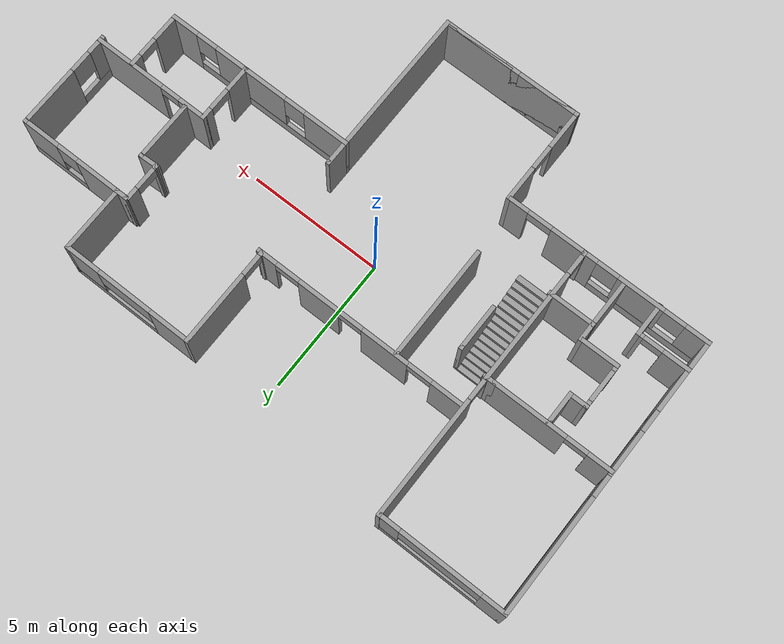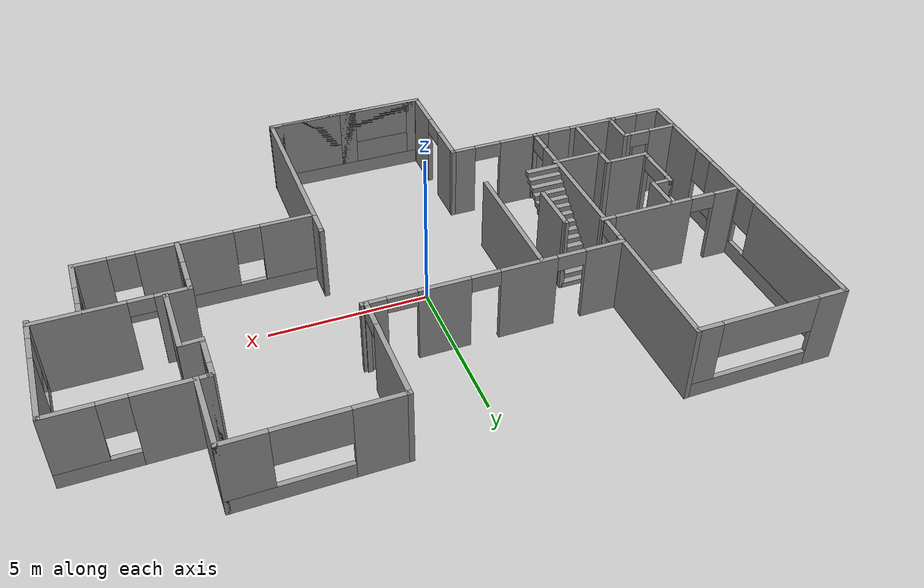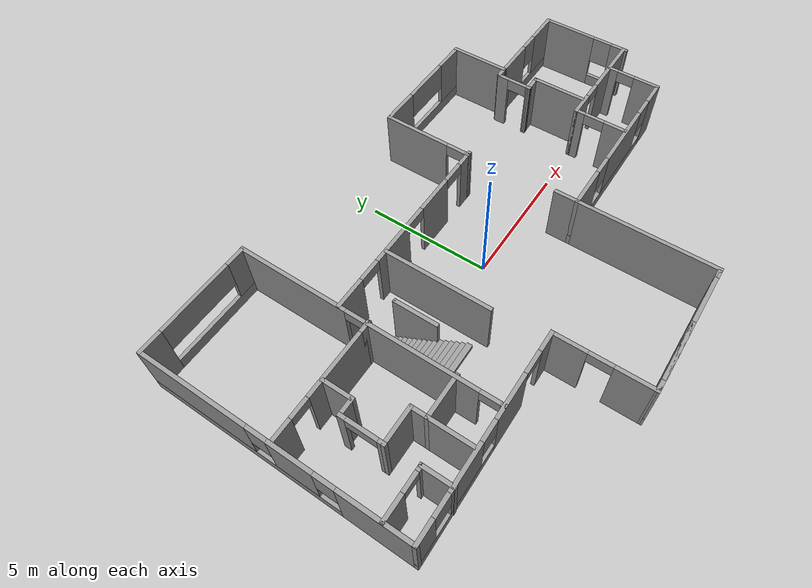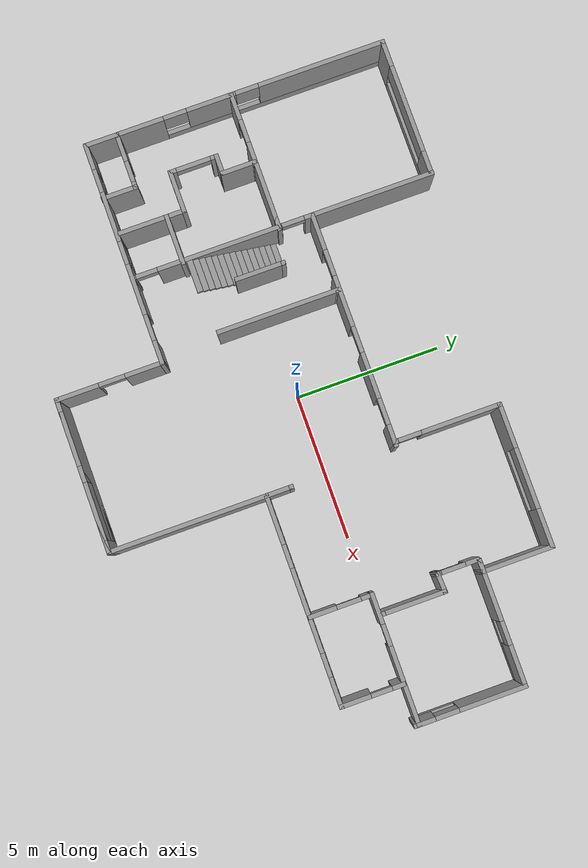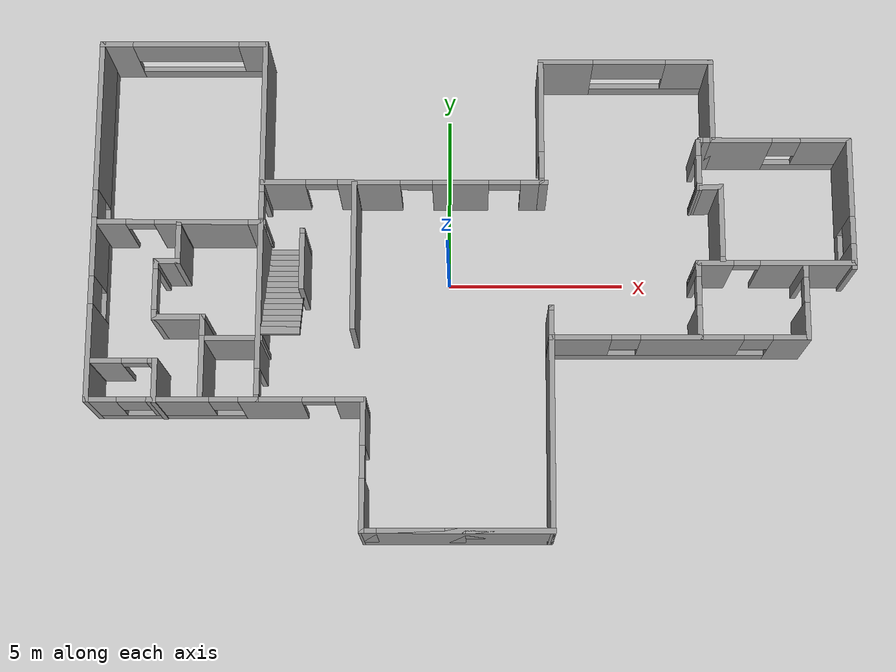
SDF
<?xml version='1.0'?>
<sdf version='1.7'>
  <model name='Floorplan5'>
    <pose>0.687179 -0.438954 0 0 -0 0</pose>
    <link name='Stairs_0'>
      <visual name='Stairs_0_Visual_0'>
        <pose>-5.3338 1.40149 0.083333 0 -0 0</pose>
        <geometry>
          <box>
            <size>1.09051 0.202493 0.166667</size>
          </box>
        </geometry>
        <material>
          <script>
            <uri>file://media/materials/scripts/gazebo.material</uri>
            <name>Gazebo/Grey</name>
          </script>
          <ambient>1 1 1 1</ambient>
        </material>
        <meta>
          <layer>0</layer>
        </meta>
      </visual>
      <collision name='Stairs_0_Collision_0'>
        <geometry>
          <box>
            <size>1.09051 0.202493 0.166667</size>
          </box>
        </geometry>
        <pose>-5.3338 1.40149 0.083333 0 -0 0</pose>
      </collision>
      <visual name='Stairs_0_Visual_1'>
        <pose>-5.3338 1.199 0.25 0 -0 0</pose>
        <geometry>
          <box>
            <size>1.09051 0.202493 0.166667</size>
          </box>
        </geometry>
        <material>
          <script>
            <uri>file://media/materials/scripts/gazebo.material</uri>
            <name>Gazebo/Grey</name>
          </script>
          <ambient>1 1 1 1</ambient>
        </material>
        <meta>
          <layer>0</layer>
        </meta>
      </visual>
      <collision name='Stairs_0_Collision_1'>
        <geometry>
          <box>
            <size>1.09051 0.202493 0.166667</size>
          </box>
        </geometry>
        <pose>-5.3338 1.199 0.25 0 -0 0</pose>
      </collision>
      <visual name='Stairs_0_Visual_2'>
        <pose>-5.3338 0.996508 0.416667 0 -0 0</pose>
        <geometry>
          <box>
            <size>1.09051 0.202493 0.166667</size>
          </box>
        </geometry>
        <material>
          <script>
            <uri>file://media/materials/scripts/gazebo.material</uri>
            <name>Gazebo/Grey</name>
          </script>
          <ambient>1 1 1 1</ambient>
        </material>
        <meta>
          <layer>0</layer>
        </meta>
      </visual>
      <collision name='Stairs_0_Collision_2'>
        <geometry>
          <box>
            <size>1.09051 0.202493 0.166667</size>
          </box>
        </geometry>
        <pose>-5.3338 0.996508 0.416667 0 -0 0</pose>
      </collision>
      <visual name='Stairs_0_Visual_3'>
        <pose>-5.3338 0.794015 0.583333 0 -0 0</pose>
        <geometry>
          <box>
            <size>1.09051 0.202493 0.166667</size>
          </box>
        </geometry>
        <material>
          <script>
            <uri>file://media/materials/scripts/gazebo.material</uri>
            <name>Gazebo/Grey</name>
          </script>
          <ambient>1 1 1 1</ambient>
        </material>
        <meta>
          <layer>0</layer>
        </meta>
      </visual>
      <collision name='Stairs_0_Collision_3'>
        <geometry>
          <box>
            <size>1.09051 0.202493 0.166667</size>
          </box>
        </geometry>
        <pose>-5.3338 0.794015 0.583333 0 -0 0</pose>
      </collision>
      <visual name='Stairs_0_Visual_4'>
        <pose>-5.3338 0.591523 0.75 0 -0 0</pose>
        <geometry>
          <box>
            <size>1.09051 0.202493 0.166667</size>
          </box>
        </geometry>
        <material>
          <script>
            <uri>file://media/materials/scripts/gazebo.material</uri>
            <name>Gazebo/Grey</name>
          </script>
          <ambient>1 1 1 1</ambient>
        </material>
        <meta>
          <layer>0</layer>
        </meta>
      </visual>
      <collision name='Stairs_0_Collision_4'>
        <geometry>
          <box>
            <size>1.09051 0.202493 0.166667</size>
          </box>
        </geometry>
        <pose>-5.3338 0.591523 0.75 0 -0 0</pose>
      </collision>
      <visual name='Stairs_0_Visual_5'>
        <pose>-5.3338 0.38903 0.916667 0 -0 0</pose>
        <geometry>
          <box>
            <size>1.09051 0.202493 0.166667</size>
          </box>
        </geometry>
        <material>
          <script>
            <uri>file://media/materials/scripts/gazebo.material</uri>
            <name>Gazebo/Grey</name>
          </script>
          <ambient>1 1 1 1</ambient>
        </material>
        <meta>
          <layer>0</layer>
        </meta>
      </visual>
      <collision name='Stairs_0_Collision_5'>
        <geometry>
          <box>
            <size>1.09051 0.202493 0.166667</size>
          </box>
        </geometry>
        <pose>-5.3338 0.38903 0.916667 0 -0 0</pose>
      </collision>
      <visual name='Stairs_0_Visual_6'>
        <pose>-5.3338 0.186538 1.08333 0 -0 0</pose>
        <geometry>
          <box>
            <size>1.09051 0.202493 0.166667</size>
          </box>
        </geometry>
        <material>
          <script>
            <uri>file://media/materials/scripts/gazebo.material</uri>
            <name>Gazebo/Grey</name>
          </script>
          <ambient>1 1 1 1</ambient>
        </material>
        <meta>
          <layer>0</layer>
        </meta>
      </visual>
      <collision name='Stairs_0_Collision_6'>
        <geometry>
          <box>
            <size>1.09051 0.202493 0.166667</size>
          </box>
        </geometry>
        <pose>-5.3338 0.186538 1.08333 0 -0 0</pose>
      </collision>
      <visual name='Stairs_0_Visual_7'>
        <pose>-5.3338 -0.015955 1.25 0 -0 0</pose>
        <geometry>
          <box>
            <size>1.09051 0.202493 0.166667</size>
          </box>
        </geometry>
        <material>
          <script>
            <uri>file://media/materials/scripts/gazebo.material</uri>
            <name>Gazebo/Grey</name>
          </script>
          <ambient>1 1 1 1</ambient>
        </material>
        <meta>
          <layer>0</layer>
        </meta>
      </visual>
      <collision name='Stairs_0_Collision_7'>
        <geometry>
          <box>
            <size>1.09051 0.202493 0.166667</size>
          </box>
        </geometry>
        <pose>-5.3338 -0.015955 1.25 0 -0 0</pose>
      </collision>
      <visual name='Stairs_0_Visual_8'>
        <pose>-5.3338 -0.218447 1.41667 0 -0 0</pose>
        <geometry>
          <box>
            <size>1.09051 0.202493 0.166667</size>
          </box>
        </geometry>
        <material>
          <script>
            <uri>file://media/materials/scripts/gazebo.material</uri>
            <name>Gazebo/Grey</name>
          </script>
          <ambient>1 1 1 1</ambient>
        </material>
        <meta>
          <layer>0</layer>
        </meta>
      </visual>
      <collision name='Stairs_0_Collision_8'>
        <geometry>
          <box>
            <size>1.09051 0.202493 0.166667</size>
          </box>
        </geometry>
        <pose>-5.3338 -0.218447 1.41667 0 -0 0</pose>
      </collision>
      <visual name='Stairs_0_Visual_9'>
        <pose>-5.3338 -0.42094 1.58333 0 -0 0</pose>
        <geometry>
          <box>
            <size>1.09051 0.202493 0.166667</size>
          </box>
        </geometry>
        <material>
          <script>
            <uri>file://media/materials/scripts/gazebo.material</uri>
            <name>Gazebo/Grey</name>
          </script>
          <ambient>1 1 1 1</ambient>
        </material>
        <meta>
          <layer>0</layer>
        </meta>
      </visual>
      <collision name='Stairs_0_Collision_9'>
        <geometry>
          <box>
            <size>1.09051 0.202493 0.166667</size>
          </box>
        </geometry>
        <pose>-5.3338 -0.42094 1.58333 0 -0 0</pose>
      </collision>
      <visual name='Stairs_0_Visual_10'>
        <pose>-5.3338 -0.623432 1.75 0 -0 0</pose>
        <geometry>
          <box>
            <size>1.09051 0.202493 0.166667</size>
          </box>
        </geometry>
        <material>
          <script>
            <uri>file://media/materials/scripts/gazebo.material</uri>
            <name>Gazebo/Grey</name>
          </script>
          <ambient>1 1 1 1</ambient>
        </material>
        <meta>
          <layer>0</layer>
        </meta>
      </visual>
      <collision name='Stairs_0_Collision_10'>
        <geometry>
          <box>
            <size>1.09051 0.202493 0.166667</size>
          </box>
        </geometry>
        <pose>-5.3338 -0.623432 1.75 0 -0 0</pose>
      </collision>
      <visual name='Stairs_0_Visual_11'>
        <pose>-5.3338 -0.825925 1.91667 0 -0 0</pose>
        <geometry>
          <box>
            <size>1.09051 0.202493 0.166667</size>
          </box>
        </geometry>
        <material>
          <script>
            <uri>file://media/materials/scripts/gazebo.material</uri>
            <name>Gazebo/Grey</name>
          </script>
          <ambient>1 1 1 1</ambient>
        </material>
        <meta>
          <layer>0</layer>
        </meta>
      </visual>
      <collision name='Stairs_0_Collision_11'>
        <geometry>
          <box>
            <size>1.09051 0.202493 0.166667</size>
          </box>
        </geometry>
        <pose>-5.3338 -0.825925 1.91667 0 -0 0</pose>
      </collision>
      <visual name='Stairs_0_Visual_12'>
        <pose>-5.3338 -1.02842 2.08333 0 -0 0</pose>
        <geometry>
          <box>
            <size>1.09051 0.202493 0.166667</size>
          </box>
        </geometry>
        <material>
          <script>
            <uri>file://media/materials/scripts/gazebo.material</uri>
            <name>Gazebo/Grey</name>
          </script>
          <ambient>1 1 1 1</ambient>
        </material>
        <meta>
          <layer>0</layer>
        </meta>
      </visual>
      <collision name='Stairs_0_Collision_12'>
        <geometry>
          <box>
            <size>1.09051 0.202493 0.166667</size>
          </box>
        </geometry>
        <pose>-5.3338 -1.02842 2.08333 0 -0 0</pose>
      </collision>
      <visual name='Stairs_0_Visual_13'>
        <pose>-5.3338 -1.23091 2.25 0 -0 0</pose>
        <geometry>
          <box>
            <size>1.09051 0.202493 0.166667</size>
          </box>
        </geometry>
        <material>
          <script>
            <uri>file://media/materials/scripts/gazebo.material</uri>
            <name>Gazebo/Grey</name>
          </script>
          <ambient>1 1 1 1</ambient>
        </material>
        <meta>
          <layer>0</layer>
        </meta>
      </visual>
      <collision name='Stairs_0_Collision_13'>
        <geometry>
          <box>
            <size>1.09051 0.202493 0.166667</size>
          </box>
        </geometry>
        <pose>-5.3338 -1.23091 2.25 0 -0 0</pose>
      </collision>
      <visual name='Stairs_0_Visual_14'>
        <pose>-5.3338 -1.4334 2.41667 0 -0 0</pose>
        <geometry>
          <box>
            <size>1.09051 0.202493 0.166667</size>
          </box>
        </geometry>
        <material>
          <script>
            <uri>file://media/materials/scripts/gazebo.material</uri>
            <name>Gazebo/Grey</name>
          </script>
          <ambient>1 1 1 1</ambient>
        </material>
        <meta>
          <layer>0</layer>
        </meta>
      </visual>
      <collision name='Stairs_0_Collision_14'>
        <geometry>
          <box>
            <size>1.09051 0.202493 0.166667</size>
          </box>
        </geometry>
        <pose>-5.3338 -1.4334 2.41667 0 -0 0</pose>
      </collision>
    </link>
    <link name='Wall_0'>
      <collision name='Wall_0_Collision'>
        <geometry>
          <box>
            <size>5.33606 0.15 2.5</size>
          </box>
        </geometry>
        <pose>0 0 1.25 0 -0 0</pose>
      </collision>
      <visual name='Wall_0_Visual'>
        <pose>0 0 1.25 0 -0 0</pose>
        <geometry>
          <box>
            <size>5.33606 0.15 2.5</size>
          </box>
        </geometry>
        <material>
          <script>
            <uri>file://media/materials/scripts/gazebo.material</uri>
            <name>Gazebo/Grey</name>
          </script>
          <ambient>1 1 1 1</ambient>
        </material>
        <meta>
          <layer>0</layer>
        </meta>
      </visual>
      <pose>-0.430466 -6.98064 0 0 -0 3.13979</pose>
    </link>
    <link name='Wall_1'>
      <pose>-3.02349 -5.17596 0 0 -0 1.5708</pose>
      <visual name='Wall_1_Visual_0'>
        <pose>-1.12311 0 1.25 0 -0 0</pose>
        <geometry>
          <box>
            <size>1.50379 0.15 2.5</size>
          </box>
        </geometry>
        <material>
          <script>
            <uri>file://media/materials/scripts/gazebo.material</uri>
            <name>Gazebo/Grey</name>
          </script>
          <ambient>1 1 1 1</ambient>
        </material>
        <meta>
          <layer>0</layer>
        </meta>
      </visual>
      <collision name='Wall_1_Collision_0'>
        <geometry>
          <box>
            <size>1.50379 0.15 2.5</size>
          </box>
        </geometry>
        <pose>-1.12311 0 1.25 0 -0 0</pose>
      </collision>
      <visual name='Wall_1_Visual_1'>
        <pose>1.20189 0 1.25 0 -0 0</pose>
        <geometry>
          <box>
            <size>1.34621 0.15 2.5</size>
          </box>
        </geometry>
        <material>
          <script>
            <uri>file://media/materials/scripts/gazebo.material</uri>
            <name>Gazebo/Grey</name>
          </script>
          <ambient>1 1 1 1</ambient>
        </material>
        <meta>
          <layer>0</layer>
        </meta>
      </visual>
      <collision name='Wall_1_Collision_1'>
        <geometry>
          <box>
            <size>1.34621 0.15 2.5</size>
          </box>
        </geometry>
        <pose>1.20189 0 1.25 0 -0 0</pose>
      </collision>
      <visual name='Wall_1_Visual_2'>
        <pose>0.078787 0 2.25 0 -0 0</pose>
        <geometry>
          <box>
            <size>0.9 0.15 0.5</size>
          </box>
        </geometry>
        <material>
          <script>
            <uri>file://media/materials/scripts/gazebo.material</uri>
            <name>Gazebo/Grey</name>
          </script>
          <ambient>1 1 1 1</ambient>
        </material>
        <meta>
          <layer>0</layer>
        </meta>
      </visual>
      <collision name='Wall_1_Collision_2'>
        <geometry>
          <box>
            <size>0.9 0.15 0.5</size>
          </box>
        </geometry>
        <pose>0.078787 0 2.25 0 -0 0</pose>
      </collision>
    </link>
    <link name='Wall_10'>
      <pose>-8.32349 6.97404 0 0 -0 0</pose>
      <visual name='Wall_10_Visual_0'>
        <pose>-1.90261 0 1.25 0 -0 0</pose>
        <geometry>
          <box>
            <size>0.944783 0.15 2.5</size>
          </box>
        </geometry>
        <material>
          <script>
            <uri>file://media/materials/scripts/gazebo.material</uri>
            <name>Gazebo/Grey</name>
          </script>
          <ambient>1 1 1 1</ambient>
        </material>
        <meta>
          <layer>0</layer>
        </meta>
      </visual>
      <collision name='Wall_10_Collision_0'>
        <geometry>
          <box>
            <size>0.944783 0.15 2.5</size>
          </box>
        </geometry>
        <pose>-1.90261 0 1.25 0 -0 0</pose>
      </collision>
      <visual name='Wall_10_Visual_1'>
        <pose>0.472392 0 0.25 0 -0 0</pose>
        <geometry>
          <box>
            <size>3.80522 0.15 0.5</size>
          </box>
        </geometry>
        <material>
          <script>
            <uri>file://media/materials/scripts/gazebo.material</uri>
            <name>Gazebo/Grey</name>
          </script>
          <ambient>1 1 1 1</ambient>
        </material>
        <meta>
          <layer>0</layer>
        </meta>
      </visual>
      <collision name='Wall_10_Collision_1'>
        <geometry>
          <box>
            <size>3.80522 0.15 0.5</size>
          </box>
        </geometry>
        <pose>0.472392 0 0.25 0 -0 0</pose>
      </collision>
      <visual name='Wall_10_Visual_2'>
        <pose>1.98492 0 1.5 0 -0 0</pose>
        <geometry>
          <box>
            <size>0.78016 0.15 2</size>
          </box>
        </geometry>
        <material>
          <script>
            <uri>file://media/materials/scripts/gazebo.material</uri>
            <name>Gazebo/Grey</name>
          </script>
          <ambient>1 1 1 1</ambient>
        </material>
        <meta>
          <layer>0</layer>
        </meta>
      </visual>
      <collision name='Wall_10_Collision_2'>
        <geometry>
          <box>
            <size>0.78016 0.15 2</size>
          </box>
        </geometry>
        <pose>1.98492 0 1.5 0 -0 0</pose>
      </collision>
      <visual name='Wall_10_Visual_3'>
        <pose>0.082312 0 1.9 0 -0 0</pose>
        <geometry>
          <box>
            <size>3.02506 0.15 1.2</size>
          </box>
        </geometry>
        <material>
          <script>
            <uri>file://media/materials/scripts/gazebo.material</uri>
            <name>Gazebo/Grey</name>
          </script>
          <ambient>1 1 1 1</ambient>
        </material>
        <meta>
          <layer>0</layer>
        </meta>
      </visual>
      <collision name='Wall_10_Collision_3'>
        <geometry>
          <box>
            <size>3.02506 0.15 1.2</size>
          </box>
        </geometry>
        <pose>0.082312 0 1.9 0 -0 0</pose>
      </collision>
    </link>
    <link name='Wall_12'>
      <pose>-2.00151 2.83994 0 0 -0 0</pose>
      <visual name='Wall_12_Visual_0'>
        <pose>-3.36386 0 1.25 0 -0 0</pose>
        <geometry>
          <box>
            <size>1.27227 0.15 2.5</size>
          </box>
        </geometry>
        <material>
          <script>
            <uri>file://media/materials/scripts/gazebo.material</uri>
            <name>Gazebo/Grey</name>
          </script>
          <ambient>1 1 1 1</ambient>
        </material>
        <meta>
          <layer>0</layer>
        </meta>
      </visual>
      <collision name='Wall_12_Collision_0'>
        <geometry>
          <box>
            <size>1.27227 0.15 2.5</size>
          </box>
        </geometry>
        <pose>-3.36386 0 1.25 0 -0 0</pose>
      </collision>
      <visual name='Wall_12_Visual_1'>
        <pose>-0.942694 0 1.25 0 -0 0</pose>
        <geometry>
          <box>
            <size>1.77007 0.15 2.5</size>
          </box>
        </geometry>
        <material>
          <script>
            <uri>file://media/materials/scripts/gazebo.material</uri>
            <name>Gazebo/Grey</name>
          </script>
          <ambient>1 1 1 1</ambient>
        </material>
        <meta>
          <layer>0</layer>
        </meta>
      </visual>
      <collision name='Wall_12_Collision_1'>
        <geometry>
          <box>
            <size>1.77007 0.15 2.5</size>
          </box>
        </geometry>
        <pose>-0.942694 0 1.25 0 -0 0</pose>
      </collision>
      <visual name='Wall_12_Visual_2'>
        <pose>1.63635 0 1.25 0 -0 0</pose>
        <geometry>
          <box>
            <size>1.58802 0.15 2.5</size>
          </box>
        </geometry>
        <material>
          <script>
            <uri>file://media/materials/scripts/gazebo.material</uri>
            <name>Gazebo/Grey</name>
          </script>
          <ambient>1 1 1 1</ambient>
        </material>
        <meta>
          <layer>0</layer>
        </meta>
      </visual>
      <collision name='Wall_12_Collision_2'>
        <geometry>
          <box>
            <size>1.58802 0.15 2.5</size>
          </box>
        </geometry>
        <pose>1.63635 0 1.25 0 -0 0</pose>
      </collision>
      <visual name='Wall_12_Visual_3'>
        <pose>3.66518 0 1.25 0 -0 0</pose>
        <geometry>
          <box>
            <size>0.669642 0.15 2.5</size>
          </box>
        </geometry>
        <material>
          <script>
            <uri>file://media/materials/scripts/gazebo.material</uri>
            <name>Gazebo/Grey</name>
          </script>
          <ambient>1 1 1 1</ambient>
        </material>
        <meta>
          <layer>0</layer>
        </meta>
      </visual>
      <collision name='Wall_12_Collision_3'>
        <geometry>
          <box>
            <size>0.669642 0.15 2.5</size>
          </box>
        </geometry>
        <pose>3.66518 0 1.25 0 -0 0</pose>
      </collision>
      <visual name='Wall_12_Visual_4'>
        <pose>-2.27773 0 2.25 0 -0 0</pose>
        <geometry>
          <box>
            <size>0.9 0.15 0.5</size>
          </box>
        </geometry>
        <material>
          <script>
            <uri>file://media/materials/scripts/gazebo.material</uri>
            <name>Gazebo/Grey</name>
          </script>
          <ambient>1 1 1 1</ambient>
        </material>
        <meta>
          <layer>0</layer>
        </meta>
      </visual>
      <collision name='Wall_12_Collision_4'>
        <geometry>
          <box>
            <size>0.9 0.15 0.5</size>
          </box>
        </geometry>
        <pose>-2.27773 0 2.25 0 -0 0</pose>
      </collision>
      <visual name='Wall_12_Visual_5'>
        <pose>0.39234 0 2.25 0 -0 0</pose>
        <geometry>
          <box>
            <size>0.9 0.15 0.5</size>
          </box>
        </geometry>
        <material>
          <script>
            <uri>file://media/materials/scripts/gazebo.material</uri>
            <name>Gazebo/Grey</name>
          </script>
          <ambient>1 1 1 1</ambient>
        </material>
        <meta>
          <layer>0</layer>
        </meta>
      </visual>
      <collision name='Wall_12_Collision_5'>
        <geometry>
          <box>
            <size>0.9 0.15 0.5</size>
          </box>
        </geometry>
        <pose>0.39234 0 2.25 0 -0 0</pose>
      </collision>
      <visual name='Wall_12_Visual_6'>
        <pose>2.88036 0 2.25 0 -0 0</pose>
        <geometry>
          <box>
            <size>0.9 0.15 0.5</size>
          </box>
        </geometry>
        <material>
          <script>
            <uri>file://media/materials/scripts/gazebo.material</uri>
            <name>Gazebo/Grey</name>
          </script>
          <ambient>1 1 1 1</ambient>
        </material>
        <meta>
          <layer>0</layer>
        </meta>
      </visual>
      <collision name='Wall_12_Collision_6'>
        <geometry>
          <box>
            <size>0.9 0.15 0.5</size>
          </box>
        </geometry>
        <pose>2.88036 0 2.25 0 -0 0</pose>
      </collision>
    </link>
    <link name='Wall_13'>
      <collision name='Wall_13_Collision'>
        <geometry>
          <box>
            <size>0.25 0.15 2.5</size>
          </box>
        </geometry>
        <pose>0 0 1.25 0 -0 0</pose>
      </collision>
      <visual name='Wall_13_Visual'>
        <pose>0 0 1.25 0 -0 0</pose>
        <geometry>
          <box>
            <size>0.25 0.15 2.5</size>
          </box>
        </geometry>
        <material>
          <script>
            <uri>file://media/materials/scripts/gazebo.material</uri>
            <name>Gazebo/Grey</name>
          </script>
          <ambient>1 1 1 1</ambient>
        </material>
        <meta>
          <layer>0</layer>
        </meta>
      </visual>
      <pose>1.97349 2.83994 0 0 -0 0</pose>
    </link>
    <link name='Wall_15'>
      <collision name='Wall_15_Collision'>
        <geometry>
          <box>
            <size>0.15 0.15 2.5</size>
          </box>
        </geometry>
        <pose>0 0 1.25 0 -0 0</pose>
      </collision>
      <visual name='Wall_15_Visual'>
        <pose>0 0 1.25 0 -0 0</pose>
        <geometry>
          <box>
            <size>0.15 0.15 2.5</size>
          </box>
        </geometry>
        <material>
          <script>
            <uri>file://media/materials/scripts/gazebo.material</uri>
            <name>Gazebo/Grey</name>
          </script>
          <ambient>1 1 1 1</ambient>
        </material>
        <meta>
          <layer>0</layer>
        </meta>
      </visual>
      <pose>1.92349 2.83994 0 0 -0 0</pose>
    </link>
    <link name='Wall_17'>
      <collision name='Wall_17_Collision'>
        <geometry>
          <box>
            <size>0.15 0.15 2.5</size>
          </box>
        </geometry>
        <pose>0 0 1.25 0 -0 0</pose>
      </collision>
      <visual name='Wall_17_Visual'>
        <pose>0 0 1.25 0 -0 0</pose>
        <geometry>
          <box>
            <size>0.15 0.15 2.5</size>
          </box>
        </geometry>
        <material>
          <script>
            <uri>file://media/materials/scripts/gazebo.material</uri>
            <name>Gazebo/Grey</name>
          </script>
          <ambient>1 1 1 1</ambient>
        </material>
        <meta>
          <layer>0</layer>
        </meta>
      </visual>
      <pose>1.92349 2.83994 0 0 -0 0</pose>
    </link>
    <link name='Wall_19'>
      <pose>1.92349 4.63994 0 0 -0 1.5708</pose>
      <visual name='Wall_19_Visual_0'>
        <pose>-1.77755 0 1.25 0 -0 0</pose>
        <geometry>
          <box>
            <size>0.19489 0.15 2.5</size>
          </box>
        </geometry>
        <material>
          <script>
            <uri>file://media/materials/scripts/gazebo.material</uri>
            <name>Gazebo/Grey</name>
          </script>
          <ambient>1 1 1 1</ambient>
        </material>
        <meta>
          <layer>0</layer>
        </meta>
      </visual>
      <collision name='Wall_19_Collision_0'>
        <geometry>
          <box>
            <size>0.19489 0.15 2.5</size>
          </box>
        </geometry>
        <pose>-1.77755 0 1.25 0 -0 0</pose>
      </collision>
      <visual name='Wall_19_Visual_1'>
        <pose>0.493912 0 1.25 0 -0 0</pose>
        <geometry>
          <box>
            <size>2.76218 0.15 2.5</size>
          </box>
        </geometry>
        <material>
          <script>
            <uri>file://media/materials/scripts/gazebo.material</uri>
            <name>Gazebo/Grey</name>
          </script>
          <ambient>1 1 1 1</ambient>
        </material>
        <meta>
          <layer>0</layer>
        </meta>
      </visual>
      <collision name='Wall_19_Collision_1'>
        <geometry>
          <box>
            <size>2.76218 0.15 2.5</size>
          </box>
        </geometry>
        <pose>0.493912 0 1.25 0 -0 0</pose>
      </collision>
      <visual name='Wall_19_Visual_2'>
        <pose>-1.28364 0 2.25 0 -0 0</pose>
        <geometry>
          <box>
            <size>0.792934 0.15 0.5</size>
          </box>
        </geometry>
        <material>
          <script>
            <uri>file://media/materials/scripts/gazebo.material</uri>
            <name>Gazebo/Grey</name>
          </script>
          <ambient>1 1 1 1</ambient>
        </material>
        <meta>
          <layer>0</layer>
        </meta>
      </visual>
      <collision name='Wall_19_Collision_2'>
        <geometry>
          <box>
            <size>0.792934 0.15 0.5</size>
          </box>
        </geometry>
        <pose>-1.28364 0 2.25 0 -0 0</pose>
      </collision>
    </link>
    <link name='Wall_20'>
      <pose>4.34849 6.43994 0 0 -0 0</pose>
      <visual name='Wall_20_Visual_0'>
        <pose>-1.71644 0 1.25 0 -0 0</pose>
        <geometry>
          <box>
            <size>1.56712 0.15 2.5</size>
          </box>
        </geometry>
        <material>
          <script>
            <uri>file://media/materials/scripts/gazebo.material</uri>
            <name>Gazebo/Grey</name>
          </script>
          <ambient>1 1 1 1</ambient>
        </material>
        <meta>
          <layer>0</layer>
        </meta>
      </visual>
      <collision name='Wall_20_Collision_0'>
        <geometry>
          <box>
            <size>1.56712 0.15 2.5</size>
          </box>
        </geometry>
        <pose>-1.71644 0 1.25 0 -0 0</pose>
      </collision>
      <visual name='Wall_20_Visual_1'>
        <pose>0.783562 0 0.25 0 -0 0</pose>
        <geometry>
          <box>
            <size>3.43288 0.15 0.5</size>
          </box>
        </geometry>
        <material>
          <script>
            <uri>file://media/materials/scripts/gazebo.material</uri>
            <name>Gazebo/Grey</name>
          </script>
          <ambient>1 1 1 1</ambient>
        </material>
        <meta>
          <layer>0</layer>
        </meta>
      </visual>
      <collision name='Wall_20_Collision_1'>
        <geometry>
          <box>
            <size>3.43288 0.15 0.5</size>
          </box>
        </geometry>
        <pose>0.783562 0 0.25 0 -0 0</pose>
      </collision>
      <visual name='Wall_20_Visual_2'>
        <pose>1.82074 0 1.5 0 -0 0</pose>
        <geometry>
          <box>
            <size>1.35853 0.15 2</size>
          </box>
        </geometry>
        <material>
          <script>
            <uri>file://media/materials/scripts/gazebo.material</uri>
            <name>Gazebo/Grey</name>
          </script>
          <ambient>1 1 1 1</ambient>
        </material>
        <meta>
          <layer>0</layer>
        </meta>
      </visual>
      <collision name='Wall_20_Collision_2'>
        <geometry>
          <box>
            <size>1.35853 0.15 2</size>
          </box>
        </geometry>
        <pose>1.82074 0 1.5 0 -0 0</pose>
      </collision>
      <visual name='Wall_20_Visual_3'>
        <pose>0.104299 0 1.9 0 -0 0</pose>
        <geometry>
          <box>
            <size>2.07435 0.15 1.2</size>
          </box>
        </geometry>
        <material>
          <script>
            <uri>file://media/materials/scripts/gazebo.material</uri>
            <name>Gazebo/Grey</name>
          </script>
          <ambient>1 1 1 1</ambient>
        </material>
        <meta>
          <layer>0</layer>
        </meta>
      </visual>
      <collision name='Wall_20_Collision_3'>
        <geometry>
          <box>
            <size>2.07435 0.15 1.2</size>
          </box>
        </geometry>
        <pose>0.104299 0 1.9 0 -0 0</pose>
      </collision>
    </link>
    <link name='Wall_21'>
      <collision name='Wall_21_Collision'>
        <geometry>
          <box>
            <size>2.5 0.15 2.5</size>
          </box>
        </geometry>
        <pose>0 0 1.25 0 -0 0</pose>
      </collision>
      <visual name='Wall_21_Visual'>
        <pose>0 0 1.25 0 -0 0</pose>
        <geometry>
          <box>
            <size>2.5 0.15 2.5</size>
          </box>
        </geometry>
        <material>
          <script>
            <uri>file://media/materials/scripts/gazebo.material</uri>
            <name>Gazebo/Grey</name>
          </script>
          <ambient>1 1 1 1</ambient>
        </material>
        <meta>
          <layer>0</layer>
        </meta>
      </visual>
      <pose>6.77349 5.26494 0 0 -0 -1.5708</pose>
    </link>
    <link name='Wall_22'>
      <collision name='Wall_22_Collision'>
        <geometry>
          <box>
            <size>0.5 0.15 2.5</size>
          </box>
        </geometry>
        <pose>0 0 1.25 0 -0 0</pose>
      </collision>
      <visual name='Wall_22_Visual'>
        <pose>0 0 1.25 0 -0 0</pose>
        <geometry>
          <box>
            <size>0.5 0.15 2.5</size>
          </box>
        </geometry>
        <material>
          <script>
            <uri>file://media/materials/scripts/gazebo.material</uri>
            <name>Gazebo/Grey</name>
          </script>
          <ambient>1 1 1 1</ambient>
        </material>
        <meta>
          <layer>0</layer>
        </meta>
      </visual>
      <pose>6.59849 4.08994 0 0 -0 3.14159</pose>
    </link>
    <link name='Wall_23'>
      <collision name='Wall_23_Collision'>
        <geometry>
          <box>
            <size>0.15 0.15 2.5</size>
          </box>
        </geometry>
        <pose>0 0 1.25 0 -0 0</pose>
      </collision>
      <visual name='Wall_23_Visual'>
        <pose>0 0 1.25 0 -0 0</pose>
        <geometry>
          <box>
            <size>0.15 0.15 2.5</size>
          </box>
        </geometry>
        <material>
          <script>
            <uri>file://media/materials/scripts/gazebo.material</uri>
            <name>Gazebo/Grey</name>
          </script>
          <ambient>1 1 1 1</ambient>
        </material>
        <meta>
          <layer>0</layer>
        </meta>
      </visual>
      <pose>6.42349 4.08994 0 0 -0 0</pose>
    </link>
    <link name='Wall_25'>
      <pose>8.69849 4.08994 0 0 -0 0</pose>
      <visual name='Wall_25_Visual_0'>
        <pose>-1.12359 0 1.25 0 -0 0</pose>
        <geometry>
          <box>
            <size>1.75281 0.15 2.5</size>
          </box>
        </geometry>
        <material>
          <script>
            <uri>file://media/materials/scripts/gazebo.material</uri>
            <name>Gazebo/Grey</name>
          </script>
          <ambient>1 1 1 1</ambient>
        </material>
        <meta>
          <layer>0</layer>
        </meta>
      </visual>
      <collision name='Wall_25_Collision_0'>
        <geometry>
          <box>
            <size>1.75281 0.15 2.5</size>
          </box>
        </geometry>
        <pose>-1.12359 0 1.25 0 -0 0</pose>
      </collision>
      <visual name='Wall_25_Visual_1'>
        <pose>0.876405 0 0.25 0 -0 0</pose>
        <geometry>
          <box>
            <size>2.24719 0.15 0.5</size>
          </box>
        </geometry>
        <material>
          <script>
            <uri>file://media/materials/scripts/gazebo.material</uri>
            <name>Gazebo/Grey</name>
          </script>
          <ambient>1 1 1 1</ambient>
        </material>
        <meta>
          <layer>0</layer>
        </meta>
      </visual>
      <collision name='Wall_25_Collision_1'>
        <geometry>
          <box>
            <size>2.24719 0.15 0.5</size>
          </box>
        </geometry>
        <pose>0.876405 0 0.25 0 -0 0</pose>
      </collision>
      <visual name='Wall_25_Visual_2'>
        <pose>1.27641 0 1.5 0 -0 0</pose>
        <geometry>
          <box>
            <size>1.44719 0.15 2</size>
          </box>
        </geometry>
        <material>
          <script>
            <uri>file://media/materials/scripts/gazebo.material</uri>
            <name>Gazebo/Grey</name>
          </script>
          <ambient>1 1 1 1</ambient>
        </material>
        <meta>
          <layer>0</layer>
        </meta>
      </visual>
      <collision name='Wall_25_Collision_2'>
        <geometry>
          <box>
            <size>1.44719 0.15 2</size>
          </box>
        </geometry>
        <pose>1.27641 0 1.5 0 -0 0</pose>
      </collision>
      <visual name='Wall_25_Visual_3'>
        <pose>0.15281 0 1.9 0 -0 0</pose>
        <geometry>
          <box>
            <size>0.8 0.15 1.2</size>
          </box>
        </geometry>
        <material>
          <script>
            <uri>file://media/materials/scripts/gazebo.material</uri>
            <name>Gazebo/Grey</name>
          </script>
          <ambient>1 1 1 1</ambient>
        </material>
        <meta>
          <layer>0</layer>
        </meta>
      </visual>
      <collision name='Wall_25_Collision_3'>
        <geometry>
          <box>
            <size>0.8 0.15 1.2</size>
          </box>
        </geometry>
        <pose>0.15281 0 1.9 0 -0 0</pose>
      </collision>
    </link>
    <link name='Wall_26'>
      <pose>10.6235 2.28994 0 0 -0 -1.5708</pose>
      <visual name='Wall_26_Visual_0'>
        <pose>-0.720844 0 1.25 0 -0 0</pose>
        <geometry>
          <box>
            <size>2.30831 0.15 2.5</size>
          </box>
        </geometry>
        <material>
          <script>
            <uri>file://media/materials/scripts/gazebo.material</uri>
            <name>Gazebo/Grey</name>
          </script>
          <ambient>1 1 1 1</ambient>
        </material>
        <meta>
          <layer>0</layer>
        </meta>
      </visual>
      <collision name='Wall_26_Collision_0'>
        <geometry>
          <box>
            <size>2.30831 0.15 2.5</size>
          </box>
        </geometry>
        <pose>-0.720844 0 1.25 0 -0 0</pose>
      </collision>
      <visual name='Wall_26_Visual_1'>
        <pose>1.15416 0 0.25 0 -0 0</pose>
        <geometry>
          <box>
            <size>1.44169 0.15 0.5</size>
          </box>
        </geometry>
        <material>
          <script>
            <uri>file://media/materials/scripts/gazebo.material</uri>
            <name>Gazebo/Grey</name>
          </script>
          <ambient>1 1 1 1</ambient>
        </material>
        <meta>
          <layer>0</layer>
        </meta>
      </visual>
      <collision name='Wall_26_Collision_1'>
        <geometry>
          <box>
            <size>1.44169 0.15 0.5</size>
          </box>
        </geometry>
        <pose>1.15416 0 0.25 0 -0 0</pose>
      </collision>
      <visual name='Wall_26_Visual_2'>
        <pose>1.55416 0 1.5 0 -0 0</pose>
        <geometry>
          <box>
            <size>0.641688 0.15 2</size>
          </box>
        </geometry>
        <material>
          <script>
            <uri>file://media/materials/scripts/gazebo.material</uri>
            <name>Gazebo/Grey</name>
          </script>
          <ambient>1 1 1 1</ambient>
        </material>
        <meta>
          <layer>0</layer>
        </meta>
      </visual>
      <collision name='Wall_26_Collision_2'>
        <geometry>
          <box>
            <size>0.641688 0.15 2</size>
          </box>
        </geometry>
        <pose>1.55416 0 1.5 0 -0 0</pose>
      </collision>
      <visual name='Wall_26_Visual_3'>
        <pose>0.833312 0 1.9 0 -0 0</pose>
        <geometry>
          <box>
            <size>0.8 0.15 1.2</size>
          </box>
        </geometry>
        <material>
          <script>
            <uri>file://media/materials/scripts/gazebo.material</uri>
            <name>Gazebo/Grey</name>
          </script>
          <ambient>1 1 1 1</ambient>
        </material>
        <meta>
          <layer>0</layer>
        </meta>
      </visual>
      <collision name='Wall_26_Collision_3'>
        <geometry>
          <box>
            <size>0.8 0.15 1.2</size>
          </box>
        </geometry>
        <pose>0.833312 0 1.9 0 -0 0</pose>
      </collision>
    </link>
    <link name='Wall_27'>
      <collision name='Wall_27_Collision'>
        <geometry>
          <box>
            <size>0.25 0.15 2.5</size>
          </box>
        </geometry>
        <pose>0 0 1.25 0 -0 0</pose>
      </collision>
      <visual name='Wall_27_Visual'>
        <pose>0 0 1.25 0 -0 0</pose>
        <geometry>
          <box>
            <size>0.25 0.15 2.5</size>
          </box>
        </geometry>
        <material>
          <script>
            <uri>file://media/materials/scripts/gazebo.material</uri>
            <name>Gazebo/Grey</name>
          </script>
          <ambient>1 1 1 1</ambient>
        </material>
        <meta>
          <layer>0</layer>
        </meta>
      </visual>
      <pose>10.6235 0.439942 0 0 -0 -1.5708</pose>
    </link>
    <link name='Wall_29'>
      <pose>8.44849 0.489942 0 0 -0 3.14159</pose>
      <visual name='Wall_29_Visual_0'>
        <pose>-0.899015 0 1.25 0 -0 0</pose>
        <geometry>
          <box>
            <size>2.70197 0.15 2.5</size>
          </box>
        </geometry>
        <material>
          <script>
            <uri>file://media/materials/scripts/gazebo.material</uri>
            <name>Gazebo/Grey</name>
          </script>
          <ambient>1 1 1 1</ambient>
        </material>
        <meta>
          <layer>0</layer>
        </meta>
      </visual>
      <collision name='Wall_29_Collision_0'>
        <geometry>
          <box>
            <size>2.70197 0.15 2.5</size>
          </box>
        </geometry>
        <pose>-0.899015 0 1.25 0 -0 0</pose>
      </collision>
      <visual name='Wall_29_Visual_1'>
        <pose>1.71686 0 1.25 0 -0 0</pose>
        <geometry>
          <box>
            <size>1.06628 0.15 2.5</size>
          </box>
        </geometry>
        <material>
          <script>
            <uri>file://media/materials/scripts/gazebo.material</uri>
            <name>Gazebo/Grey</name>
          </script>
          <ambient>1 1 1 1</ambient>
        </material>
        <meta>
          <layer>0</layer>
        </meta>
      </visual>
      <collision name='Wall_29_Collision_1'>
        <geometry>
          <box>
            <size>1.06628 0.15 2.5</size>
          </box>
        </geometry>
        <pose>1.71686 0 1.25 0 -0 0</pose>
      </collision>
      <visual name='Wall_29_Visual_2'>
        <pose>0.817847 0 2.25 0 -0 0</pose>
        <geometry>
          <box>
            <size>0.731754 0.15 0.5</size>
          </box>
        </geometry>
        <material>
          <script>
            <uri>file://media/materials/scripts/gazebo.material</uri>
            <name>Gazebo/Grey</name>
          </script>
          <ambient>1 1 1 1</ambient>
        </material>
        <meta>
          <layer>0</layer>
        </meta>
      </visual>
      <collision name='Wall_29_Collision_2'>
        <geometry>
          <box>
            <size>0.731754 0.15 0.5</size>
          </box>
        </geometry>
        <pose>0.817847 0 2.25 0 -0 0</pose>
      </collision>
    </link>
    <link name='Wall_30'>
      <collision name='Wall_30_Collision'>
        <geometry>
          <box>
            <size>0.15 0.15 2.5</size>
          </box>
        </geometry>
        <pose>0 0 1.25 0 -0 0</pose>
      </collision>
      <visual name='Wall_30_Visual'>
        <pose>0 0 1.25 0 -0 0</pose>
        <geometry>
          <box>
            <size>0.15 0.15 2.5</size>
          </box>
        </geometry>
        <material>
          <script>
            <uri>file://media/materials/scripts/gazebo.material</uri>
            <name>Gazebo/Grey</name>
          </script>
          <ambient>1 1 1 1</ambient>
        </material>
        <meta>
          <layer>0</layer>
        </meta>
      </visual>
      <pose>6.27349 0.489942 0 0 -0 0</pose>
    </link>
    <link name='Wall_32'>
      <pose>6.36151 3.36099 0 0 -0 -1.5708</pose>
      <visual name='Wall_32_Visual_0'>
        <pose>-0.510408 0 1.25 0 -0 0</pose>
        <geometry>
          <box>
            <size>0.479183 0.15 2.5</size>
          </box>
        </geometry>
        <material>
          <script>
            <uri>file://media/materials/scripts/gazebo.material</uri>
            <name>Gazebo/Grey</name>
          </script>
          <ambient>1 1 1 1</ambient>
        </material>
        <meta>
          <layer>0</layer>
        </meta>
      </visual>
      <collision name='Wall_32_Collision_0'>
        <geometry>
          <box>
            <size>0.479183 0.15 2.5</size>
          </box>
        </geometry>
        <pose>-0.510408 0 1.25 0 -0 0</pose>
      </collision>
      <visual name='Wall_32_Visual_1'>
        <pose>0.650239 0 1.25 0 -0 0</pose>
        <geometry>
          <box>
            <size>0.199522 0.15 2.5</size>
          </box>
        </geometry>
        <material>
          <script>
            <uri>file://media/materials/scripts/gazebo.material</uri>
            <name>Gazebo/Grey</name>
          </script>
          <ambient>1 1 1 1</ambient>
        </material>
        <meta>
          <layer>0</layer>
        </meta>
      </visual>
      <collision name='Wall_32_Collision_1'>
        <geometry>
          <box>
            <size>0.199522 0.15 2.5</size>
          </box>
        </geometry>
        <pose>0.650239 0 1.25 0 -0 0</pose>
      </collision>
      <visual name='Wall_32_Visual_2'>
        <pose>0.139831 0 2.25 0 -0 0</pose>
        <geometry>
          <box>
            <size>0.821295 0.15 0.5</size>
          </box>
        </geometry>
        <material>
          <script>
            <uri>file://media/materials/scripts/gazebo.material</uri>
            <name>Gazebo/Grey</name>
          </script>
          <ambient>1 1 1 1</ambient>
        </material>
        <meta>
          <layer>0</layer>
        </meta>
      </visual>
      <collision name='Wall_32_Collision_2'>
        <geometry>
          <box>
            <size>0.821295 0.15 0.5</size>
          </box>
        </geometry>
        <pose>0.139831 0 2.25 0 -0 0</pose>
      </collision>
    </link>
    <link name='Wall_33'>
      <collision name='Wall_33_Collision'>
        <geometry>
          <box>
            <size>0.75 0.15 2.5</size>
          </box>
        </geometry>
        <pose>0 0 1.25 0 -0 0</pose>
      </collision>
      <visual name='Wall_33_Visual'>
        <pose>0 0 1.25 0 -0 0</pose>
        <geometry>
          <box>
            <size>0.75 0.15 2.5</size>
          </box>
        </geometry>
        <material>
          <script>
            <uri>file://media/materials/scripts/gazebo.material</uri>
            <name>Gazebo/Grey</name>
          </script>
          <ambient>1 1 1 1</ambient>
        </material>
        <meta>
          <layer>0</layer>
        </meta>
      </visual>
      <pose>6.66151 2.69929 0 0 -0 0.044305</pose>
    </link>
    <link name='Wall_34'>
      <collision name='Wall_34_Collision'>
        <geometry>
          <box>
            <size>2.25 0.15 2.5</size>
          </box>
        </geometry>
        <pose>0 0 1.25 0 -0 0</pose>
      </collision>
      <visual name='Wall_34_Visual'>
        <pose>0 0 1.25 0 -0 0</pose>
        <geometry>
          <box>
            <size>2.25 0.15 2.5</size>
          </box>
        </geometry>
        <material>
          <script>
            <uri>file://media/materials/scripts/gazebo.material</uri>
            <name>Gazebo/Grey</name>
          </script>
          <ambient>1 1 1 1</ambient>
        </material>
        <meta>
          <layer>0</layer>
        </meta>
      </visual>
      <pose>6.96151 1.64929 0 0 -0 -1.5708</pose>
    </link>
    <link name='Wall_35'>
      <collision name='Wall_35_Collision'>
        <geometry>
          <box>
            <size>0.15 0.15 2.5</size>
          </box>
        </geometry>
        <pose>0 0 1.25 0 -0 0</pose>
      </collision>
      <visual name='Wall_35_Visual'>
        <pose>0 0 1.25 0 -0 0</pose>
        <geometry>
          <box>
            <size>0.15 0.15 2.5</size>
          </box>
        </geometry>
        <material>
          <script>
            <uri>file://media/materials/scripts/gazebo.material</uri>
            <name>Gazebo/Grey</name>
          </script>
          <ambient>1 1 1 1</ambient>
        </material>
        <meta>
          <layer>0</layer>
        </meta>
      </visual>
      <pose>6.96151 0.612589 0 0 -0 0</pose>
    </link>
    <link name='Wall_37'>
      <pose>9.26256 -0.585315 0 0 -0 -1.5708</pose>
      <visual name='Wall_37_Visual_0'>
        <pose>-0.899951 0 1.25 0 -0 0</pose>
        <geometry>
          <box>
            <size>0.450099 0.15 2.5</size>
          </box>
        </geometry>
        <material>
          <script>
            <uri>file://media/materials/scripts/gazebo.material</uri>
            <name>Gazebo/Grey</name>
          </script>
          <ambient>1 1 1 1</ambient>
        </material>
        <meta>
          <layer>0</layer>
        </meta>
      </visual>
      <collision name='Wall_37_Collision_0'>
        <geometry>
          <box>
            <size>0.450099 0.15 2.5</size>
          </box>
        </geometry>
        <pose>-0.899951 0 1.25 0 -0 0</pose>
      </collision>
      <visual name='Wall_37_Visual_1'>
        <pose>0.583279 0 1.25 0 -0 0</pose>
        <geometry>
          <box>
            <size>1.08344 0.15 2.5</size>
          </box>
        </geometry>
        <material>
          <script>
            <uri>file://media/materials/scripts/gazebo.material</uri>
            <name>Gazebo/Grey</name>
          </script>
          <ambient>1 1 1 1</ambient>
        </material>
        <meta>
          <layer>0</layer>
        </meta>
      </visual>
      <collision name='Wall_37_Collision_1'>
        <geometry>
          <box>
            <size>1.08344 0.15 2.5</size>
          </box>
        </geometry>
        <pose>0.583279 0 1.25 0 -0 0</pose>
      </collision>
      <visual name='Wall_37_Visual_2'>
        <pose>-0.316672 0 2.25 0 -0 0</pose>
        <geometry>
          <box>
            <size>0.716459 0.15 0.5</size>
          </box>
        </geometry>
        <material>
          <script>
            <uri>file://media/materials/scripts/gazebo.material</uri>
            <name>Gazebo/Grey</name>
          </script>
          <ambient>1 1 1 1</ambient>
        </material>
        <meta>
          <layer>0</layer>
        </meta>
      </visual>
      <collision name='Wall_37_Collision_2'>
        <geometry>
          <box>
            <size>0.716459 0.15 0.5</size>
          </box>
        </geometry>
        <pose>-0.316672 0 2.25 0 -0 0</pose>
      </collision>
    </link>
    <link name='Wall_38'>
      <pose>5.71256 -1.63532 0 0 -0 3.14159</pose>
      <visual name='Wall_38_Visual_0'>
        <pose>-3.0964 0 1.25 0 -0 0</pose>
        <geometry>
          <box>
            <size>1.05719 0.15 2.5</size>
          </box>
        </geometry>
        <material>
          <script>
            <uri>file://media/materials/scripts/gazebo.material</uri>
            <name>Gazebo/Grey</name>
          </script>
          <ambient>1 1 1 1</ambient>
        </material>
        <meta>
          <layer>0</layer>
        </meta>
      </visual>
      <collision name='Wall_38_Collision_0'>
        <geometry>
          <box>
            <size>1.05719 0.15 2.5</size>
          </box>
        </geometry>
        <pose>-3.0964 0 1.25 0 -0 0</pose>
      </collision>
      <visual name='Wall_38_Visual_1'>
        <pose>0.528596 0 0.25 0 -0 0</pose>
        <geometry>
          <box>
            <size>6.19281 0.15 0.5</size>
          </box>
        </geometry>
        <material>
          <script>
            <uri>file://media/materials/scripts/gazebo.material</uri>
            <name>Gazebo/Grey</name>
          </script>
          <ambient>1 1 1 1</ambient>
        </material>
        <meta>
          <layer>0</layer>
        </meta>
      </visual>
      <collision name='Wall_38_Collision_1'>
        <geometry>
          <box>
            <size>6.19281 0.15 0.5</size>
          </box>
        </geometry>
        <pose>0.528596 0 0.25 0 -0 0</pose>
      </collision>
      <visual name='Wall_38_Visual_2'>
        <pose>-0.337194 0 1.5 0 -0 0</pose>
        <geometry>
          <box>
            <size>2.86123 0.15 2</size>
          </box>
        </geometry>
        <material>
          <script>
            <uri>file://media/materials/scripts/gazebo.material</uri>
            <name>Gazebo/Grey</name>
          </script>
          <ambient>1 1 1 1</ambient>
        </material>
        <meta>
          <layer>0</layer>
        </meta>
      </visual>
      <collision name='Wall_38_Collision_2'>
        <geometry>
          <box>
            <size>2.86123 0.15 2</size>
          </box>
        </geometry>
        <pose>-0.337194 0 1.5 0 -0 0</pose>
      </collision>
      <visual name='Wall_38_Visual_3'>
        <pose>2.75921 0 1.5 0 -0 0</pose>
        <geometry>
          <box>
            <size>1.73158 0.15 2</size>
          </box>
        </geometry>
        <material>
          <script>
            <uri>file://media/materials/scripts/gazebo.material</uri>
            <name>Gazebo/Grey</name>
          </script>
          <ambient>1 1 1 1</ambient>
        </material>
        <meta>
          <layer>0</layer>
        </meta>
      </visual>
      <collision name='Wall_38_Collision_3'>
        <geometry>
          <box>
            <size>1.73158 0.15 2</size>
          </box>
        </geometry>
        <pose>2.75921 0 1.5 0 -0 0</pose>
      </collision>
      <visual name='Wall_38_Visual_4'>
        <pose>-2.16781 0 1.9 0 -0 0</pose>
        <geometry>
          <box>
            <size>0.8 0.15 1.2</size>
          </box>
        </geometry>
        <material>
          <script>
            <uri>file://media/materials/scripts/gazebo.material</uri>
            <name>Gazebo/Grey</name>
          </script>
          <ambient>1 1 1 1</ambient>
        </material>
        <meta>
          <layer>0</layer>
        </meta>
      </visual>
      <collision name='Wall_38_Collision_4'>
        <geometry>
          <box>
            <size>0.8 0.15 1.2</size>
          </box>
        </geometry>
        <pose>-2.16781 0 1.9 0 -0 0</pose>
      </collision>
      <visual name='Wall_38_Visual_5'>
        <pose>1.49342 0 1.9 0 -0 0</pose>
        <geometry>
          <box>
            <size>0.8 0.15 1.2</size>
          </box>
        </geometry>
        <material>
          <script>
            <uri>file://media/materials/scripts/gazebo.material</uri>
            <name>Gazebo/Grey</name>
          </script>
          <ambient>1 1 1 1</ambient>
        </material>
        <meta>
          <layer>0</layer>
        </meta>
      </visual>
      <collision name='Wall_38_Collision_5'>
        <geometry>
          <box>
            <size>0.8 0.15 1.2</size>
          </box>
        </geometry>
        <pose>1.49342 0 1.9 0 -0 0</pose>
      </collision>
    </link>
    <link name='Wall_39'>
      <collision name='Wall_39_Collision'>
        <geometry>
          <box>
            <size>1 0.15 2.5</size>
          </box>
        </geometry>
        <pose>0 0 1.25 0 -0 0</pose>
      </collision>
      <visual name='Wall_39_Visual'>
        <pose>0 0 1.25 0 -0 0</pose>
        <geometry>
          <box>
            <size>1 0.15 2.5</size>
          </box>
        </geometry>
        <material>
          <script>
            <uri>file://media/materials/scripts/gazebo.material</uri>
            <name>Gazebo/Grey</name>
          </script>
          <ambient>1 1 1 1</ambient>
        </material>
        <meta>
          <layer>0</layer>
        </meta>
      </visual>
      <pose>2.16256 -1.21032 0 0 -0 1.5708</pose>
    </link>
    <link name='Wall_40'>
      <collision name='Wall_40_Collision'>
        <geometry>
          <box>
            <size>0.15 0.15 2.5</size>
          </box>
        </geometry>
        <pose>0 0 1.25 0 -0 0</pose>
      </collision>
      <visual name='Wall_40_Visual'>
        <pose>0 0 1.25 0 -0 0</pose>
        <geometry>
          <box>
            <size>0.15 0.15 2.5</size>
          </box>
        </geometry>
        <material>
          <script>
            <uri>file://media/materials/scripts/gazebo.material</uri>
            <name>Gazebo/Grey</name>
          </script>
          <ambient>1 1 1 1</ambient>
        </material>
        <meta>
          <layer>0</layer>
        </meta>
      </visual>
      <pose>2.16256 -0.785315 0 0 -0 0</pose>
    </link>
    <link name='Wall_42'>
      <collision name='Wall_42_Collision'>
        <geometry>
          <box>
            <size>5.5 0.15 2.5</size>
          </box>
        </geometry>
        <pose>0 0 1.25 0 -0 0</pose>
      </collision>
      <visual name='Wall_42_Visual'>
        <pose>0 0 1.25 0 -0 0</pose>
        <geometry>
          <box>
            <size>5.5 0.15 2.5</size>
          </box>
        </geometry>
        <material>
          <script>
            <uri>file://media/materials/scripts/gazebo.material</uri>
            <name>Gazebo/Grey</name>
          </script>
          <ambient>1 1 1 1</ambient>
        </material>
        <meta>
          <layer>0</layer>
        </meta>
      </visual>
      <pose>2.16256 -4.31032 0 0 -0 -1.5708</pose>
    </link>
    <link name='Wall_43'>
      <pose>-0.430466 -6.98064 0 0 -0 3.13979</pose>
      <visual name='Wall_43_Visual_0'>
        <pose>-2.44294 0 1.25 0 -0 0</pose>
        <geometry>
          <box>
            <size>0.450176 0.15 2.5</size>
          </box>
        </geometry>
        <material>
          <script>
            <uri>file://media/materials/scripts/gazebo.material</uri>
            <name>Gazebo/Grey</name>
          </script>
          <ambient>1 1 1 1</ambient>
        </material>
        <meta>
          <layer>0</layer>
        </meta>
      </visual>
      <collision name='Wall_43_Collision_0'>
        <geometry>
          <box>
            <size>0.450176 0.15 2.5</size>
          </box>
        </geometry>
        <pose>-2.44294 0 1.25 0 -0 0</pose>
      </collision>
      <visual name='Wall_43_Visual_1'>
        <pose>0.225088 0 0.25 0 -0 0</pose>
        <geometry>
          <box>
            <size>4.88588 0.15 0.5</size>
          </box>
        </geometry>
        <material>
          <script>
            <uri>file://media/materials/scripts/gazebo.material</uri>
            <name>Gazebo/Grey</name>
          </script>
          <ambient>1 1 1 1</ambient>
        </material>
        <meta>
          <layer>0</layer>
        </meta>
      </visual>
      <collision name='Wall_43_Collision_1'>
        <geometry>
          <box>
            <size>4.88588 0.15 0.5</size>
          </box>
        </geometry>
        <pose>0.225088 0 0.25 0 -0 0</pose>
      </collision>
      <visual name='Wall_43_Visual_2'>
        <pose>0.053397 0 1.5 0 -0 0</pose>
        <geometry>
          <box>
            <size>0.555406 0.15 2</size>
          </box>
        </geometry>
        <material>
          <script>
            <uri>file://media/materials/scripts/gazebo.material</uri>
            <name>Gazebo/Grey</name>
          </script>
          <ambient>1 1 1 1</ambient>
        </material>
        <meta>
          <layer>0</layer>
        </meta>
      </visual>
      <collision name='Wall_43_Collision_2'>
        <geometry>
          <box>
            <size>0.555406 0.15 2</size>
          </box>
        </geometry>
        <pose>0.053397 0 1.5 0 -0 0</pose>
      </collision>
      <visual name='Wall_43_Visual_3'>
        <pose>2.42547 0 1.5 0 -0 0</pose>
        <geometry>
          <box>
            <size>0.485123 0.15 2</size>
          </box>
        </geometry>
        <material>
          <script>
            <uri>file://media/materials/scripts/gazebo.material</uri>
            <name>Gazebo/Grey</name>
          </script>
          <ambient>1 1 1 1</ambient>
        </material>
        <meta>
          <layer>0</layer>
        </meta>
      </visual>
      <collision name='Wall_43_Collision_3'>
        <geometry>
          <box>
            <size>0.485123 0.15 2</size>
          </box>
        </geometry>
        <pose>2.42547 0 1.5 0 -0 0</pose>
      </collision>
      <visual name='Wall_43_Visual_4'>
        <pose>-1.22108 0 1.9 0 -0 0</pose>
        <geometry>
          <box>
            <size>1.99355 0.15 1.2</size>
          </box>
        </geometry>
        <material>
          <script>
            <uri>file://media/materials/scripts/gazebo.material</uri>
            <name>Gazebo/Grey</name>
          </script>
          <ambient>1 1 1 1</ambient>
        </material>
        <meta>
          <layer>0</layer>
        </meta>
      </visual>
      <collision name='Wall_43_Collision_4'>
        <geometry>
          <box>
            <size>1.99355 0.15 1.2</size>
          </box>
        </geometry>
        <pose>-1.22108 0 1.9 0 -0 0</pose>
      </collision>
      <visual name='Wall_43_Visual_5'>
        <pose>1.257 0 1.9 0 -0 0</pose>
        <geometry>
          <box>
            <size>1.85181 0.15 1.2</size>
          </box>
        </geometry>
        <material>
          <script>
            <uri>file://media/materials/scripts/gazebo.material</uri>
            <name>Gazebo/Grey</name>
          </script>
          <ambient>1 1 1 1</ambient>
        </material>
        <meta>
          <layer>0</layer>
        </meta>
      </visual>
      <collision name='Wall_43_Collision_5'>
        <geometry>
          <box>
            <size>1.85181 0.15 1.2</size>
          </box>
        </geometry>
        <pose>1.257 0 1.9 0 -0 0</pose>
      </collision>
    </link>
    <link name='Wall_44'>
      <collision name='Wall_44_Collision'>
        <geometry>
          <box>
            <size>0.16 0.15 2.5</size>
          </box>
        </geometry>
        <pose>0 0 1.25 0 -0 0</pose>
      </collision>
      <visual name='Wall_44_Visual'>
        <pose>0 0 1.25 0 -0 0</pose>
        <geometry>
          <box>
            <size>0.16 0.15 2.5</size>
          </box>
        </geometry>
        <material>
          <script>
            <uri>file://media/materials/scripts/gazebo.material</uri>
            <name>Gazebo/Grey</name>
          </script>
          <ambient>1 1 1 1</ambient>
        </material>
        <meta>
          <layer>0</layer>
        </meta>
      </visual>
      <pose>-3.01849 -6.97596 0 0 -0 0</pose>
    </link>
    <link name='Wall_46'>
      <pose>6.27349 -0.560058 0 0 -0 -1.5708</pose>
      <visual name='Wall_46_Visual_0'>
        <pose>-0.898794 0 1.25 0 -0 0</pose>
        <geometry>
          <box>
            <size>0.452413 0.15 2.5</size>
          </box>
        </geometry>
        <material>
          <script>
            <uri>file://media/materials/scripts/gazebo.material</uri>
            <name>Gazebo/Grey</name>
          </script>
          <ambient>1 1 1 1</ambient>
        </material>
        <meta>
          <layer>0</layer>
        </meta>
      </visual>
      <collision name='Wall_46_Collision_0'>
        <geometry>
          <box>
            <size>0.452413 0.15 2.5</size>
          </box>
        </geometry>
        <pose>-0.898794 0 1.25 0 -0 0</pose>
      </collision>
      <visual name='Wall_46_Visual_1'>
        <pose>0.637969 0 1.25 0 -0 0</pose>
        <geometry>
          <box>
            <size>0.974063 0.15 2.5</size>
          </box>
        </geometry>
        <material>
          <script>
            <uri>file://media/materials/scripts/gazebo.material</uri>
            <name>Gazebo/Grey</name>
          </script>
          <ambient>1 1 1 1</ambient>
        </material>
        <meta>
          <layer>0</layer>
        </meta>
      </visual>
      <collision name='Wall_46_Collision_1'>
        <geometry>
          <box>
            <size>0.974063 0.15 2.5</size>
          </box>
        </geometry>
        <pose>0.637969 0 1.25 0 -0 0</pose>
      </collision>
      <visual name='Wall_46_Visual_2'>
        <pose>-0.260825 0 2.25 0 -0 0</pose>
        <geometry>
          <box>
            <size>0.823524 0.15 0.5</size>
          </box>
        </geometry>
        <material>
          <script>
            <uri>file://media/materials/scripts/gazebo.material</uri>
            <name>Gazebo/Grey</name>
          </script>
          <ambient>1 1 1 1</ambient>
        </material>
        <meta>
          <layer>0</layer>
        </meta>
      </visual>
      <collision name='Wall_46_Collision_2'>
        <geometry>
          <box>
            <size>0.823524 0.15 0.5</size>
          </box>
        </geometry>
        <pose>-0.260825 0 2.25 0 -0 0</pose>
      </collision>
    </link>
    <link name='Wall_47'>
      <collision name='Wall_47_Collision'>
        <geometry>
          <box>
            <size>0.15 0.15 2.5</size>
          </box>
        </geometry>
        <pose>0 0 1.25 0 -0 0</pose>
      </collision>
      <visual name='Wall_47_Visual'>
        <pose>0 0 1.25 0 -0 0</pose>
        <geometry>
          <box>
            <size>0.15 0.15 2.5</size>
          </box>
        </geometry>
        <material>
          <script>
            <uri>file://media/materials/scripts/gazebo.material</uri>
            <name>Gazebo/Grey</name>
          </script>
          <ambient>1 1 1 1</ambient>
        </material>
        <meta>
          <layer>0</layer>
        </meta>
      </visual>
      <pose>6.27349 -1.61006 0 0 -0 0</pose>
    </link>
    <link name='Wall_49'>
      <collision name='Wall_49_Collision'>
        <geometry>
          <box>
            <size>4.25 0.15 2.5</size>
          </box>
        </geometry>
        <pose>0 0 1.25 0 -0 0</pose>
      </collision>
      <visual name='Wall_49_Visual'>
        <pose>0 0 1.25 0 -0 0</pose>
        <geometry>
          <box>
            <size>4.25 0.15 2.5</size>
          </box>
        </geometry>
        <material>
          <script>
            <uri>file://media/materials/scripts/gazebo.material</uri>
            <name>Gazebo/Grey</name>
          </script>
          <ambient>1 1 1 1</ambient>
        </material>
        <meta>
          <layer>0</layer>
        </meta>
      </visual>
      <pose>-3.34876 0.736864 0 0 -0 1.5708</pose>
    </link>
    <link name='Wall_5'>
      <pose>-5.95393 1.81045 0 0 -0 -1.5708</pose>
      <visual name='Wall_5_Visual_0'>
        <pose>-2.99965 0 1.25 0 -0 0</pose>
        <geometry>
          <box>
            <size>4.50069 0.15 2.5</size>
          </box>
        </geometry>
        <material>
          <script>
            <uri>file://media/materials/scripts/gazebo.material</uri>
            <name>Gazebo/Grey</name>
          </script>
          <ambient>1 1 1 1</ambient>
        </material>
        <meta>
          <layer>0</layer>
        </meta>
      </visual>
      <collision name='Wall_5_Collision_0'>
        <geometry>
          <box>
            <size>4.50069 0.15 2.5</size>
          </box>
        </geometry>
        <pose>-2.99965 0 1.25 0 -0 0</pose>
      </collision>
      <visual name='Wall_5_Visual_1'>
        <pose>2.1786 0 1.25 0 -0 0</pose>
        <geometry>
          <box>
            <size>4.29854 0.15 2.5</size>
          </box>
        </geometry>
        <material>
          <script>
            <uri>file://media/materials/scripts/gazebo.material</uri>
            <name>Gazebo/Grey</name>
          </script>
          <ambient>1 1 1 1</ambient>
        </material>
        <meta>
          <layer>0</layer>
        </meta>
      </visual>
      <collision name='Wall_5_Collision_1'>
        <geometry>
          <box>
            <size>4.29854 0.15 2.5</size>
          </box>
        </geometry>
        <pose>2.1786 0 1.25 0 -0 0</pose>
      </collision>
      <visual name='Wall_5_Visual_2'>
        <pose>5.15802 0 1.25 0 -0 0</pose>
        <geometry>
          <box>
            <size>0.183955 0.15 2.5</size>
          </box>
        </geometry>
        <material>
          <script>
            <uri>file://media/materials/scripts/gazebo.material</uri>
            <name>Gazebo/Grey</name>
          </script>
          <ambient>1 1 1 1</ambient>
        </material>
        <meta>
          <layer>0</layer>
        </meta>
      </visual>
      <collision name='Wall_5_Collision_2'>
        <geometry>
          <box>
            <size>0.183955 0.15 2.5</size>
          </box>
        </geometry>
        <pose>5.15802 0 1.25 0 -0 0</pose>
      </collision>
      <visual name='Wall_5_Visual_3'>
        <pose>-0.359991 0 2.25 0 -0 0</pose>
        <geometry>
          <box>
            <size>0.778633 0.15 0.5</size>
          </box>
        </geometry>
        <material>
          <script>
            <uri>file://media/materials/scripts/gazebo.material</uri>
            <name>Gazebo/Grey</name>
          </script>
          <ambient>1 1 1 1</ambient>
        </material>
        <meta>
          <layer>0</layer>
        </meta>
      </visual>
      <collision name='Wall_5_Collision_3'>
        <geometry>
          <box>
            <size>0.778633 0.15 0.5</size>
          </box>
        </geometry>
        <pose>-0.359991 0 2.25 0 -0 0</pose>
      </collision>
      <visual name='Wall_5_Visual_4'>
        <pose>4.69696 0 2.25 0 -0 0</pose>
        <geometry>
          <box>
            <size>0.738178 0.15 0.5</size>
          </box>
        </geometry>
        <material>
          <script>
            <uri>file://media/materials/scripts/gazebo.material</uri>
            <name>Gazebo/Grey</name>
          </script>
          <ambient>1 1 1 1</ambient>
        </material>
        <meta>
          <layer>0</layer>
        </meta>
      </visual>
      <collision name='Wall_5_Collision_4'>
        <geometry>
          <box>
            <size>0.738178 0.15 0.5</size>
          </box>
        </geometry>
        <pose>4.69696 0 2.25 0 -0 0</pose>
      </collision>
    </link>
    <link name='Wall_50'>
      <collision name='Wall_50_Collision'>
        <geometry>
          <box>
            <size>0.15 0.15 2.5</size>
          </box>
        </geometry>
        <pose>0 0 1.25 0 -0 0</pose>
      </collision>
      <visual name='Wall_50_Visual'>
        <pose>0 0 1.25 0 -0 0</pose>
        <geometry>
          <box>
            <size>0.15 0.15 2.5</size>
          </box>
        </geometry>
        <material>
          <script>
            <uri>file://media/materials/scripts/gazebo.material</uri>
            <name>Gazebo/Grey</name>
          </script>
          <ambient>1 1 1 1</ambient>
        </material>
        <meta>
          <layer>0</layer>
        </meta>
      </visual>
      <pose>-3.34876 2.78686 0 0 -0 0</pose>
    </link>
    <link name='Wall_52'>
      <pose>-8.41531 1.68058 0 0 -0 0</pose>
      <visual name='Wall_52_Visual_0'>
        <pose>-1.78515 0 1.25 0 -0 0</pose>
        <geometry>
          <box>
            <size>0.929692 0.15 2.5</size>
          </box>
        </geometry>
        <material>
          <script>
            <uri>file://media/materials/scripts/gazebo.material</uri>
            <name>Gazebo/Grey</name>
          </script>
          <ambient>1 1 1 1</ambient>
        </material>
        <meta>
          <layer>0</layer>
        </meta>
      </visual>
      <collision name='Wall_52_Collision_0'>
        <geometry>
          <box>
            <size>0.929692 0.15 2.5</size>
          </box>
        </geometry>
        <pose>-1.78515 0 1.25 0 -0 0</pose>
      </collision>
      <visual name='Wall_52_Visual_1'>
        <pose>0.864277 0 1.25 0 -0 0</pose>
        <geometry>
          <box>
            <size>2.77145 0.15 2.5</size>
          </box>
        </geometry>
        <material>
          <script>
            <uri>file://media/materials/scripts/gazebo.material</uri>
            <name>Gazebo/Grey</name>
          </script>
          <ambient>1 1 1 1</ambient>
        </material>
        <meta>
          <layer>0</layer>
        </meta>
      </visual>
      <collision name='Wall_52_Collision_1'>
        <geometry>
          <box>
            <size>2.77145 0.15 2.5</size>
          </box>
        </geometry>
        <pose>0.864277 0 1.25 0 -0 0</pose>
      </collision>
      <visual name='Wall_52_Visual_2'>
        <pose>-0.920877 0 2.25 0 -0 0</pose>
        <geometry>
          <box>
            <size>0.798861 0.15 0.5</size>
          </box>
        </geometry>
        <material>
          <script>
            <uri>file://media/materials/scripts/gazebo.material</uri>
            <name>Gazebo/Grey</name>
          </script>
          <ambient>1 1 1 1</ambient>
        </material>
        <meta>
          <layer>0</layer>
        </meta>
      </visual>
      <collision name='Wall_52_Collision_2'>
        <geometry>
          <box>
            <size>0.798861 0.15 0.5</size>
          </box>
        </geometry>
        <pose>-0.920877 0 2.25 0 -0 0</pose>
      </collision>
    </link>
    <link name='Wall_53'>
      <collision name='Wall_53_Collision'>
        <geometry>
          <box>
            <size>0.5 0.15 2.5</size>
          </box>
        </geometry>
        <pose>0 0 1.25 0 -0 0</pose>
      </collision>
      <visual name='Wall_53_Visual'>
        <pose>0 0 1.25 0 -0 0</pose>
        <geometry>
          <box>
            <size>0.5 0.15 2.5</size>
          </box>
        </geometry>
        <material>
          <script>
            <uri>file://media/materials/scripts/gazebo.material</uri>
            <name>Gazebo/Grey</name>
          </script>
          <ambient>1 1 1 1</ambient>
        </material>
        <meta>
          <layer>0</layer>
        </meta>
      </visual>
      <pose>-6.06531 1.68058 0 0 -0 0</pose>
    </link>
    <link name='Wall_54'>
      <collision name='Wall_54_Collision'>
        <geometry>
          <box>
            <size>0.15 0.15 2.5</size>
          </box>
        </geometry>
        <pose>0 0 1.25 0 -0 0</pose>
      </collision>
      <visual name='Wall_54_Visual'>
        <pose>0 0 1.25 0 -0 0</pose>
        <geometry>
          <box>
            <size>0.15 0.15 2.5</size>
          </box>
        </geometry>
        <material>
          <script>
            <uri>file://media/materials/scripts/gazebo.material</uri>
            <name>Gazebo/Grey</name>
          </script>
          <ambient>1 1 1 1</ambient>
        </material>
        <meta>
          <layer>0</layer>
        </meta>
      </visual>
      <pose>-5.89031 1.68058 0 0 -0 0</pose>
    </link>
    <link name='Wall_56'>
      <collision name='Wall_56_Collision'>
        <geometry>
          <box>
            <size>1.75 0.15 2.5</size>
          </box>
        </geometry>
        <pose>0 0 1.25 0 -0 0</pose>
      </collision>
      <visual name='Wall_56_Visual'>
        <pose>0 0 1.25 0 -0 0</pose>
        <geometry>
          <box>
            <size>1.75 0.15 2.5</size>
          </box>
        </geometry>
        <material>
          <script>
            <uri>file://media/materials/scripts/gazebo.material</uri>
            <name>Gazebo/Grey</name>
          </script>
          <ambient>1 1 1 1</ambient>
        </material>
        <meta>
          <layer>0</layer>
        </meta>
      </visual>
      <pose>-6.69746 -1.65701 0 0 -0 3.14159</pose>
    </link>
    <link name='Wall_57'>
      <collision name='Wall_57_Collision'>
        <geometry>
          <box>
            <size>1.75 0.15 2.5</size>
          </box>
        </geometry>
        <pose>0 0 1.25 0 -0 0</pose>
      </collision>
      <visual name='Wall_57_Visual'>
        <pose>0 0 1.25 0 -0 0</pose>
        <geometry>
          <box>
            <size>1.75 0.15 2.5</size>
          </box>
        </geometry>
        <material>
          <script>
            <uri>file://media/materials/scripts/gazebo.material</uri>
            <name>Gazebo/Grey</name>
          </script>
          <ambient>1 1 1 1</ambient>
        </material>
        <meta>
          <layer>0</layer>
        </meta>
      </visual>
      <pose>-7.49746 -2.45701 0 0 -0 -1.5708</pose>
    </link>
    <link name='Wall_59'>
      <collision name='Wall_59_Collision'>
        <geometry>
          <box>
            <size>0.75 0.15 2.5</size>
          </box>
        </geometry>
        <pose>0 0 1.25 0 -0 0</pose>
      </collision>
      <visual name='Wall_59_Visual'>
        <pose>0 0 1.25 0 -0 0</pose>
        <geometry>
          <box>
            <size>0.75 0.15 2.5</size>
          </box>
        </geometry>
        <material>
          <script>
            <uri>file://media/materials/scripts/gazebo.material</uri>
            <name>Gazebo/Grey</name>
          </script>
          <ambient>1 1 1 1</ambient>
        </material>
        <meta>
          <layer>0</layer>
        </meta>
      </visual>
      <pose>-7.49746 -1.35701 0 0 -0 1.5708</pose>
    </link>
    <link name='Wall_6'>
      <collision name='Wall_6_Collision'>
        <geometry>
          <box>
            <size>0.15 0.15 2.5</size>
          </box>
        </geometry>
        <pose>0 0 1.25 0 -0 0</pose>
      </collision>
      <visual name='Wall_6_Visual'>
        <pose>0 0 1.25 0 -0 0</pose>
        <geometry>
          <box>
            <size>0.15 0.15 2.5</size>
          </box>
        </geometry>
        <material>
          <script>
            <uri>file://media/materials/scripts/gazebo.material</uri>
            <name>Gazebo/Grey</name>
          </script>
          <ambient>1 1 1 1</ambient>
        </material>
        <meta>
          <layer>0</layer>
        </meta>
      </visual>
      <pose>-5.95393 -3.37335 0 0 -0 0</pose>
    </link>
    <link name='Wall_60'>
      <collision name='Wall_60_Collision'>
        <geometry>
          <box>
            <size>1.5 0.15 2.5</size>
          </box>
        </geometry>
        <pose>0 0 1.25 0 -0 0</pose>
      </collision>
      <visual name='Wall_60_Visual'>
        <pose>0 0 1.25 0 -0 0</pose>
        <geometry>
          <box>
            <size>1.5 0.15 2.5</size>
          </box>
        </geometry>
        <material>
          <script>
            <uri>file://media/materials/scripts/gazebo.material</uri>
            <name>Gazebo/Grey</name>
          </script>
          <ambient>1 1 1 1</ambient>
        </material>
        <meta>
          <layer>0</layer>
        </meta>
      </visual>
      <pose>-8.17246 -1.05701 0 0 -0 3.14159</pose>
    </link>
    <link name='Wall_61'>
      <pose>-8.84746 -0.257008 0 0 -0 1.5708</pose>
      <visual name='Wall_61_Visual_0'>
        <pose>-0.735439 0 1.25 0 -0 0</pose>
        <geometry>
          <box>
            <size>0.279123 0.15 2.5</size>
          </box>
        </geometry>
        <material>
          <script>
            <uri>file://media/materials/scripts/gazebo.material</uri>
            <name>Gazebo/Grey</name>
          </script>
          <ambient>1 1 1 1</ambient>
        </material>
        <meta>
          <layer>0</layer>
        </meta>
      </visual>
      <collision name='Wall_61_Collision_0'>
        <geometry>
          <box>
            <size>0.279123 0.15 2.5</size>
          </box>
        </geometry>
        <pose>-0.735439 0 1.25 0 -0 0</pose>
      </collision>
      <visual name='Wall_61_Visual_1'>
        <pose>0.731156 0 1.25 0 -0 0</pose>
        <geometry>
          <box>
            <size>0.287688 0.15 2.5</size>
          </box>
        </geometry>
        <material>
          <script>
            <uri>file://media/materials/scripts/gazebo.material</uri>
            <name>Gazebo/Grey</name>
          </script>
          <ambient>1 1 1 1</ambient>
        </material>
        <meta>
          <layer>0</layer>
        </meta>
      </visual>
      <collision name='Wall_61_Collision_1'>
        <geometry>
          <box>
            <size>0.287688 0.15 2.5</size>
          </box>
        </geometry>
        <pose>0.731156 0 1.25 0 -0 0</pose>
      </collision>
      <visual name='Wall_61_Visual_2'>
        <pose>-0.004283 0 2.25 0 -0 0</pose>
        <geometry>
          <box>
            <size>1.18319 0.15 0.5</size>
          </box>
        </geometry>
        <material>
          <script>
            <uri>file://media/materials/scripts/gazebo.material</uri>
            <name>Gazebo/Grey</name>
          </script>
          <ambient>1 1 1 1</ambient>
        </material>
        <meta>
          <layer>0</layer>
        </meta>
      </visual>
      <collision name='Wall_61_Collision_2'>
        <geometry>
          <box>
            <size>1.18319 0.15 0.5</size>
          </box>
        </geometry>
        <pose>-0.004283 0 2.25 0 -0 0</pose>
      </collision>
    </link>
    <link name='Wall_62'>
      <collision name='Wall_62_Collision'>
        <geometry>
          <box>
            <size>0.75 0.15 2.5</size>
          </box>
        </geometry>
        <pose>0 0 1.25 0 -0 0</pose>
      </collision>
      <visual name='Wall_62_Visual'>
        <pose>0 0 1.25 0 -0 0</pose>
        <geometry>
          <box>
            <size>0.75 0.15 2.5</size>
          </box>
        </geometry>
        <material>
          <script>
            <uri>file://media/materials/scripts/gazebo.material</uri>
            <name>Gazebo/Grey</name>
          </script>
          <ambient>1 1 1 1</ambient>
        </material>
        <meta>
          <layer>0</layer>
        </meta>
      </visual>
      <pose>-8.54746 0.542992 0 0 -0 0</pose>
    </link>
    <link name='Wall_63'>
      <collision name='Wall_63_Collision'>
        <geometry>
          <box>
            <size>1.25 0.15 2.5</size>
          </box>
        </geometry>
        <pose>0 0 1.25 0 -0 0</pose>
      </collision>
      <visual name='Wall_63_Visual'>
        <pose>0 0 1.25 0 -0 0</pose>
        <geometry>
          <box>
            <size>1.25 0.15 2.5</size>
          </box>
        </geometry>
        <material>
          <script>
            <uri>file://media/materials/scripts/gazebo.material</uri>
            <name>Gazebo/Grey</name>
          </script>
          <ambient>1 1 1 1</ambient>
        </material>
        <meta>
          <layer>0</layer>
        </meta>
      </visual>
      <pose>-8.24746 1.09299 0 0 -0 1.5708</pose>
    </link>
    <link name='Wall_64'>
      <collision name='Wall_64_Collision'>
        <geometry>
          <box>
            <size>0.15 0.15 2.5</size>
          </box>
        </geometry>
        <pose>0 0 1.25 0 -0 0</pose>
      </collision>
      <visual name='Wall_64_Visual'>
        <pose>0 0 1.25 0 -0 0</pose>
        <geometry>
          <box>
            <size>0.15 0.15 2.5</size>
          </box>
        </geometry>
        <material>
          <script>
            <uri>file://media/materials/scripts/gazebo.material</uri>
            <name>Gazebo/Grey</name>
          </script>
          <ambient>1 1 1 1</ambient>
        </material>
        <meta>
          <layer>0</layer>
        </meta>
      </visual>
      <pose>-8.24746 1.64299 0 0 -0 0</pose>
    </link>
    <link name='Wall_66'>
      <collision name='Wall_66_Collision'>
        <geometry>
          <box>
            <size>1.25 0.15 2.5</size>
          </box>
        </geometry>
        <pose>0 0 1.25 0 -0 0</pose>
      </collision>
      <visual name='Wall_66_Visual'>
        <pose>0 0 1.25 0 -0 0</pose>
        <geometry>
          <box>
            <size>1.25 0.15 2.5</size>
          </box>
        </geometry>
        <material>
          <script>
            <uri>file://media/materials/scripts/gazebo.material</uri>
            <name>Gazebo/Grey</name>
          </script>
          <ambient>1 1 1 1</ambient>
        </material>
        <meta>
          <layer>0</layer>
        </meta>
      </visual>
      <pose>-8.7698 -2.8466 0 0 -0 1.5708</pose>
    </link>
    <link name='Wall_67'>
      <pose>-9.69481 -2.2966 0 0 -0 3.14159</pose>
      <visual name='Wall_67_Visual_0'>
        <pose>-0.863855 0 1.25 0 -0 0</pose>
        <geometry>
          <box>
            <size>0.27229 0.15 2.5</size>
          </box>
        </geometry>
        <material>
          <script>
            <uri>file://media/materials/scripts/gazebo.material</uri>
            <name>Gazebo/Grey</name>
          </script>
          <ambient>1 1 1 1</ambient>
        </material>
        <meta>
          <layer>0</layer>
        </meta>
      </visual>
      <collision name='Wall_67_Collision_0'>
        <geometry>
          <box>
            <size>0.27229 0.15 2.5</size>
          </box>
        </geometry>
        <pose>-0.863855 0 1.25 0 -0 0</pose>
      </collision>
      <visual name='Wall_67_Visual_1'>
        <pose>0.49512 0 1.25 0 -0 0</pose>
        <geometry>
          <box>
            <size>1.00976 0.15 2.5</size>
          </box>
        </geometry>
        <material>
          <script>
            <uri>file://media/materials/scripts/gazebo.material</uri>
            <name>Gazebo/Grey</name>
          </script>
          <ambient>1 1 1 1</ambient>
        </material>
        <meta>
          <layer>0</layer>
        </meta>
      </visual>
      <collision name='Wall_67_Collision_1'>
        <geometry>
          <box>
            <size>1.00976 0.15 2.5</size>
          </box>
        </geometry>
        <pose>0.49512 0 1.25 0 -0 0</pose>
      </collision>
      <visual name='Wall_67_Visual_2'>
        <pose>-0.368735 0 2.25 0 -0 0</pose>
        <geometry>
          <box>
            <size>0.71795 0.15 0.5</size>
          </box>
        </geometry>
        <material>
          <script>
            <uri>file://media/materials/scripts/gazebo.material</uri>
            <name>Gazebo/Grey</name>
          </script>
          <ambient>1 1 1 1</ambient>
        </material>
        <meta>
          <layer>0</layer>
        </meta>
      </visual>
      <collision name='Wall_67_Collision_2'>
        <geometry>
          <box>
            <size>0.71795 0.15 0.5</size>
          </box>
        </geometry>
        <pose>-0.368735 0 2.25 0 -0 0</pose>
      </collision>
    </link>
    <link name='Wall_68'>
      <collision name='Wall_68_Collision'>
        <geometry>
          <box>
            <size>0.16 0.15 2.5</size>
          </box>
        </geometry>
        <pose>0 0 1.25 0 -0 0</pose>
      </collision>
      <visual name='Wall_68_Visual'>
        <pose>0 0 1.25 0 -0 0</pose>
        <geometry>
          <box>
            <size>0.16 0.15 2.5</size>
          </box>
        </geometry>
        <material>
          <script>
            <uri>file://media/materials/scripts/gazebo.material</uri>
            <name>Gazebo/Grey</name>
          </script>
          <ambient>1 1 1 1</ambient>
        </material>
        <meta>
          <layer>0</layer>
        </meta>
      </visual>
      <pose>-10.6148 -2.2966 0 0 -0 0</pose>
    </link>
    <link name='Wall_70'>
      <collision name='Wall_70_Collision'>
        <geometry>
          <box>
            <size>1.75 0.15 2.5</size>
          </box>
        </geometry>
        <pose>0 0 1.25 0 -0 0</pose>
      </collision>
      <visual name='Wall_70_Visual'>
        <pose>0 0 1.25 0 -0 0</pose>
        <geometry>
          <box>
            <size>1.75 0.15 2.5</size>
          </box>
        </geometry>
        <material>
          <script>
            <uri>file://media/materials/scripts/gazebo.material</uri>
            <name>Gazebo/Grey</name>
          </script>
          <ambient>1 1 1 1</ambient>
        </material>
        <meta>
          <layer>0</layer>
        </meta>
      </visual>
      <pose>-4.78493 0.61962 0 0 -0 1.5708</pose>
    </link>
    <link name='Wall_71'>
      <collision name='Wall_71_Collision'>
        <geometry>
          <box>
            <size>0.15 0.15 2.5</size>
          </box>
        </geometry>
        <pose>0 0 1.25 0 -0 0</pose>
      </collision>
      <visual name='Wall_71_Visual'>
        <pose>0 0 1.25 0 -0 0</pose>
        <geometry>
          <box>
            <size>0.15 0.15 2.5</size>
          </box>
        </geometry>
        <material>
          <script>
            <uri>file://media/materials/scripts/gazebo.material</uri>
            <name>Gazebo/Grey</name>
          </script>
          <ambient>1 1 1 1</ambient>
        </material>
        <meta>
          <layer>0</layer>
        </meta>
      </visual>
      <pose>-4.78493 1.41962 0 0 -0 0</pose>
    </link>
    <link name='Wall_8'>
      <pose>-6.82349 -3.37596 0 0 -0 3.14159</pose>
      <visual name='Wall_8_Visual_0'>
        <pose>-3.45485 0 1.25 0 -0 0</pose>
        <geometry>
          <box>
            <size>0.84029 0.15 2.5</size>
          </box>
        </geometry>
        <material>
          <script>
            <uri>file://media/materials/scripts/gazebo.material</uri>
            <name>Gazebo/Grey</name>
          </script>
          <ambient>1 1 1 1</ambient>
        </material>
        <meta>
          <layer>0</layer>
        </meta>
      </visual>
      <collision name='Wall_8_Collision_0'>
        <geometry>
          <box>
            <size>0.84029 0.15 2.5</size>
          </box>
        </geometry>
        <pose>-3.45485 0 1.25 0 -0 0</pose>
      </collision>
      <visual name='Wall_8_Visual_1'>
        <pose>-1.25637 0 1.25 0 -0 0</pose>
        <geometry>
          <box>
            <size>1.75668 0.15 2.5</size>
          </box>
        </geometry>
        <material>
          <script>
            <uri>file://media/materials/scripts/gazebo.material</uri>
            <name>Gazebo/Grey</name>
          </script>
          <ambient>1 1 1 1</ambient>
        </material>
        <meta>
          <layer>0</layer>
        </meta>
      </visual>
      <collision name='Wall_8_Collision_1'>
        <geometry>
          <box>
            <size>1.75668 0.15 2.5</size>
          </box>
        </geometry>
        <pose>-1.25637 0 1.25 0 -0 0</pose>
      </collision>
      <visual name='Wall_8_Visual_2'>
        <pose>1.74849 0 0.25 0 -0 0</pose>
        <geometry>
          <box>
            <size>4.25303 0.15 0.5</size>
          </box>
        </geometry>
        <material>
          <script>
            <uri>file://media/materials/scripts/gazebo.material</uri>
            <name>Gazebo/Grey</name>
          </script>
          <ambient>1 1 1 1</ambient>
        </material>
        <meta>
          <layer>0</layer>
        </meta>
      </visual>
      <collision name='Wall_8_Collision_2'>
        <geometry>
          <box>
            <size>4.25303 0.15 0.5</size>
          </box>
        </geometry>
        <pose>1.74849 0 0.25 0 -0 0</pose>
      </collision>
      <visual name='Wall_8_Visual_3'>
        <pose>1.28621 0 1.5 0 -0 0</pose>
        <geometry>
          <box>
            <size>1.72847 0.15 2</size>
          </box>
        </geometry>
        <material>
          <script>
            <uri>file://media/materials/scripts/gazebo.material</uri>
            <name>Gazebo/Grey</name>
          </script>
          <ambient>1 1 1 1</ambient>
        </material>
        <meta>
          <layer>0</layer>
        </meta>
      </visual>
      <collision name='Wall_8_Collision_3'>
        <geometry>
          <box>
            <size>1.72847 0.15 2</size>
          </box>
        </geometry>
        <pose>1.28621 0 1.5 0 -0 0</pose>
      </collision>
      <visual name='Wall_8_Visual_4'>
        <pose>3.41272 0 1.5 0 -0 0</pose>
        <geometry>
          <box>
            <size>0.924556 0.15 2</size>
          </box>
        </geometry>
        <material>
          <script>
            <uri>file://media/materials/scripts/gazebo.material</uri>
            <name>Gazebo/Grey</name>
          </script>
          <ambient>1 1 1 1</ambient>
        </material>
        <meta>
          <layer>0</layer>
        </meta>
      </visual>
      <collision name='Wall_8_Collision_4'>
        <geometry>
          <box>
            <size>0.924556 0.15 2</size>
          </box>
        </geometry>
        <pose>3.41272 0 1.5 0 -0 0</pose>
      </collision>
      <visual name='Wall_8_Visual_5'>
        <pose>0.021971 0 1.9 0 -0 0</pose>
        <geometry>
          <box>
            <size>0.8 0.15 1.2</size>
          </box>
        </geometry>
        <material>
          <script>
            <uri>file://media/materials/scripts/gazebo.material</uri>
            <name>Gazebo/Grey</name>
          </script>
          <ambient>1 1 1 1</ambient>
        </material>
        <meta>
          <layer>0</layer>
        </meta>
      </visual>
      <collision name='Wall_8_Collision_5'>
        <geometry>
          <box>
            <size>0.8 0.15 1.2</size>
          </box>
        </geometry>
        <pose>0.021971 0 1.9 0 -0 0</pose>
      </collision>
      <visual name='Wall_8_Visual_6'>
        <pose>2.55044 0 1.9 0 -0 0</pose>
        <geometry>
          <box>
            <size>0.8 0.15 1.2</size>
          </box>
        </geometry>
        <material>
          <script>
            <uri>file://media/materials/scripts/gazebo.material</uri>
            <name>Gazebo/Grey</name>
          </script>
          <ambient>1 1 1 1</ambient>
        </material>
        <meta>
          <layer>0</layer>
        </meta>
      </visual>
      <collision name='Wall_8_Collision_6'>
        <geometry>
          <box>
            <size>0.8 0.15 1.2</size>
          </box>
        </geometry>
        <pose>2.55044 0 1.9 0 -0 0</pose>
      </collision>
      <visual name='Wall_8_Visual_7'>
        <pose>-2.58471 0 2.25 0 -0 0</pose>
        <geometry>
          <box>
            <size>0.9 0.15 0.5</size>
          </box>
        </geometry>
        <material>
          <script>
            <uri>file://media/materials/scripts/gazebo.material</uri>
            <name>Gazebo/Grey</name>
          </script>
          <ambient>1 1 1 1</ambient>
        </material>
        <meta>
          <layer>0</layer>
        </meta>
      </visual>
      <collision name='Wall_8_Collision_7'>
        <geometry>
          <box>
            <size>0.9 0.15 0.5</size>
          </box>
        </geometry>
        <pose>-2.58471 0 2.25 0 -0 0</pose>
      </collision>
    </link>
    <link name='Wall_9'>
      <pose>-10.6235 1.79904 0 0 -0 1.5708</pose>
      <visual name='Wall_9_Visual_0'>
        <pose>-3.866 0 1.25 0 -0 0</pose>
        <geometry>
          <box>
            <size>2.768 0.15 2.5</size>
          </box>
        </geometry>
        <material>
          <script>
            <uri>file://media/materials/scripts/gazebo.material</uri>
            <name>Gazebo/Grey</name>
          </script>
          <ambient>1 1 1 1</ambient>
        </material>
        <meta>
          <layer>0</layer>
        </meta>
      </visual>
      <collision name='Wall_9_Collision_0'>
        <geometry>
          <box>
            <size>2.768 0.15 2.5</size>
          </box>
        </geometry>
        <pose>-3.866 0 1.25 0 -0 0</pose>
      </collision>
      <visual name='Wall_9_Visual_1'>
        <pose>1.384 0 0.25 0 -0 0</pose>
        <geometry>
          <box>
            <size>7.732 0.15 0.5</size>
          </box>
        </geometry>
        <material>
          <script>
            <uri>file://media/materials/scripts/gazebo.material</uri>
            <name>Gazebo/Grey</name>
          </script>
          <ambient>1 1 1 1</ambient>
        </material>
        <meta>
          <layer>0</layer>
        </meta>
      </visual>
      <collision name='Wall_9_Collision_1'>
        <geometry>
          <box>
            <size>7.732 0.15 0.5</size>
          </box>
        </geometry>
        <pose>1.384 0 0.25 0 -0 0</pose>
      </collision>
      <visual name='Wall_9_Visual_2'>
        <pose>-0.827877 0 1.5 0 -0 0</pose>
        <geometry>
          <box>
            <size>1.70825 0.15 2</size>
          </box>
        </geometry>
        <material>
          <script>
            <uri>file://media/materials/scripts/gazebo.material</uri>
            <name>Gazebo/Grey</name>
          </script>
          <ambient>1 1 1 1</ambient>
        </material>
        <meta>
          <layer>0</layer>
        </meta>
      </visual>
      <collision name='Wall_9_Collision_2'>
        <geometry>
          <box>
            <size>1.70825 0.15 2</size>
          </box>
        </geometry>
        <pose>-0.827877 0 1.5 0 -0 0</pose>
      </collision>
      <visual name='Wall_9_Visual_3'>
        <pose>3.03812 0 1.5 0 -0 0</pose>
        <geometry>
          <box>
            <size>4.42375 0.15 2</size>
          </box>
        </geometry>
        <material>
          <script>
            <uri>file://media/materials/scripts/gazebo.material</uri>
            <name>Gazebo/Grey</name>
          </script>
          <ambient>1 1 1 1</ambient>
        </material>
        <meta>
          <layer>0</layer>
        </meta>
      </visual>
      <collision name='Wall_9_Collision_3'>
        <geometry>
          <box>
            <size>4.42375 0.15 2</size>
          </box>
        </geometry>
        <pose>3.03812 0 1.5 0 -0 0</pose>
      </collision>
      <visual name='Wall_9_Visual_4'>
        <pose>-2.082 0 1.9 0 -0 0</pose>
        <geometry>
          <box>
            <size>0.8 0.15 1.2</size>
          </box>
        </geometry>
        <material>
          <script>
            <uri>file://media/materials/scripts/gazebo.material</uri>
            <name>Gazebo/Grey</name>
          </script>
          <ambient>1 1 1 1</ambient>
        </material>
        <meta>
          <layer>0</layer>
        </meta>
      </visual>
      <collision name='Wall_9_Collision_4'>
        <geometry>
          <box>
            <size>0.8 0.15 1.2</size>
          </box>
        </geometry>
        <pose>-2.082 0 1.9 0 -0 0</pose>
      </collision>
      <visual name='Wall_9_Visual_5'>
        <pose>0.426246 0 1.9 0 -0 0</pose>
        <geometry>
          <box>
            <size>0.8 0.15 1.2</size>
          </box>
        </geometry>
        <material>
          <script>
            <uri>file://media/materials/scripts/gazebo.material</uri>
            <name>Gazebo/Grey</name>
          </script>
          <ambient>1 1 1 1</ambient>
        </material>
        <meta>
          <layer>0</layer>
        </meta>
      </visual>
      <collision name='Wall_9_Collision_5'>
        <geometry>
          <box>
            <size>0.8 0.15 1.2</size>
          </box>
        </geometry>
        <pose>0.426246 0 1.9 0 -0 0</pose>
      </collision>
    </link>
    <static>1</static>
  </model>
</sdf>
